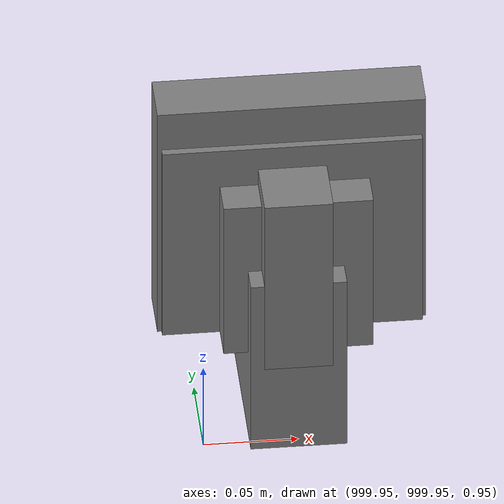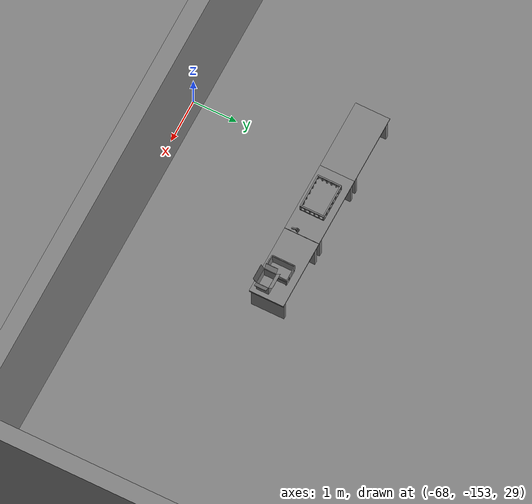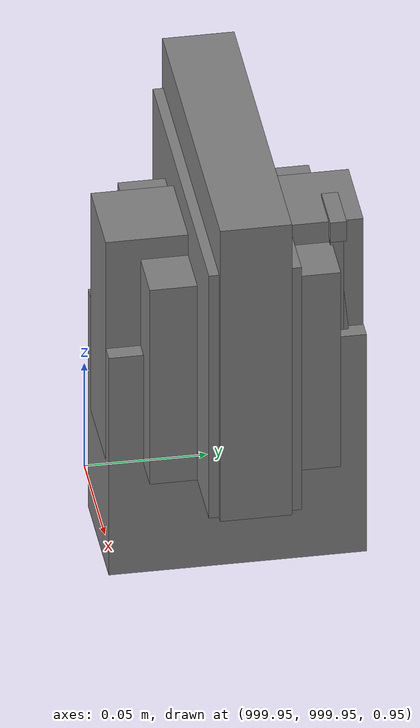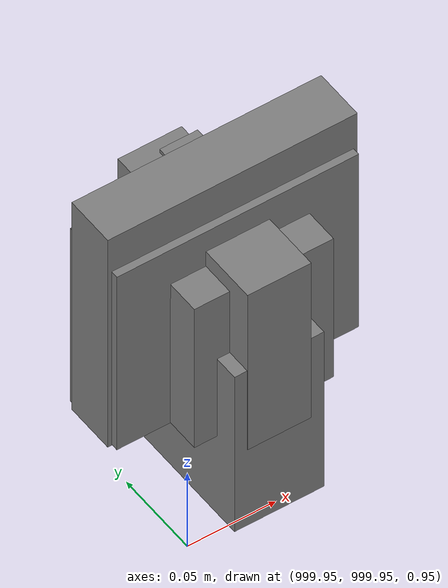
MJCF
<mujoco>
    <option gravity="0.000000000 0.000000000 -9.810000420" timestep="0.0049999999" integrator="implicitfast" density="1.225" viscosity="1.8000001e-05" noslip_iterations="10" iterations="100" sdf_iterations="50">
        <flag multiccd="disable"/>
    </option>
    <size memory="1000M"/>
    <compiler coordinate="local"/>
    <worldbody>
        <light cutoff="30" pos="0 1 1" dir="0 -1 -2"/>
        <light cutoff="30" pos="0 -1 1" dir="0 1 -2"/>
        <body pos="-64.866622925 -149.383972168 30.183746338" euler="89.999984741 89.999946594 0.000000000" name="openloong_gripper_2f85_fix_base_usda_bluebox_01">
            <geom contype="1" conaffinity="1" density="1000" type="box" material="" rgba="0.500000000 0.500000000 0.500000000 1.000000000" solimp="0.899999976 0.949999988 0.001000000" friction="1.000000000 0.005000000 0.000100000" solref="0.020000000 1.000000000" margin="0" condim="3" group="0" pos="0.276580811 0.187225342 0.000068665" quat="0.707106948 0.000077471 0.707106352 0.000077486" size="0.100000001 0.057999998 0.010000000" name="openloong_gripper_2f85_fix_base_usda_geom_FB6A63C0_ED59_477A_85FF_AAF391F5D108"/>
            <geom contype="1" conaffinity="1" density="1000" type="box" material="" rgba="0.500000000 0.500000000 0.500000000 1.000000000" solimp="0.899999976 0.949999988 0.001000000" friction="1.000000000 0.005000000 0.000100000" solref="0.020000000 1.000000000" margin="0" condim="3" group="0" pos="0.000000000 0.002883911 0.000000000" quat="0.999999881 0.000000000 0.000000000 0.000000000" size="0.254000008 0.003000000 0.172000006" name="openloong_gripper_2f85_fix_base_usda_geom_891953E2_4AC2_4312_A1DF_9480A01B147F"/>
            <geom contype="1" conaffinity="1" density="1000" type="box" material="" rgba="0.500000000 0.500000000 0.500000000 1.000000000" solimp="0.899999976 0.949999988 0.001000000" friction="1.000000000 0.005000000 0.000100000" solref="0.020000000 1.000000000" margin="0" condim="3" group="0" pos="0.000000000 0.124874115 0.173484802" quat="0.999796331 0.020176515 -0.000000015 0.000000030" size="0.259999990 0.119999997 0.007000000" name="openloong_gripper_2f85_fix_base_usda_geom_57A227EB_34C0_4F8B_8F18_470882F73B1E"/>
            <geom contype="1" conaffinity="1" density="1000" type="box" material="" rgba="0.500000000 0.500000000 0.500000000 1.000000000" solimp="0.899999976 0.949999988 0.001000000" friction="1.000000000 0.005000000 0.000100000" solref="0.020000000 1.000000000" margin="0" condim="3" group="0" pos="0.000000000 0.124874115 -0.173469543" quat="0.999796331 -0.020176545 -0.000000015 0.000000000" size="0.259999990 0.119999997 0.007000000" name="openloong_gripper_2f85_fix_base_usda_geom_81F08663_940D_484F_A97E_80766AC8F83D"/>
            <geom contype="1" conaffinity="1" density="1000" type="box" material="" rgba="0.500000000 0.500000000 0.500000000 1.000000000" solimp="0.899999976 0.949999988 0.001000000" friction="1.000000000 0.005000000 0.000100000" solref="0.020000000 1.000000000" margin="0" condim="3" group="0" pos="0.000000000 0.214008331 0.188980103" quat="0.999912977 0.013176724 0.000000015 0.000000000" size="0.259999990 0.029999999 0.012500000" name="openloong_gripper_2f85_fix_base_usda_geom_15919A1A_FCBE_49DE_B51F_51EDFA0D06FF"/>
            <geom contype="1" conaffinity="1" density="1000" type="box" material="" rgba="0.500000000 0.500000000 0.500000000 1.000000000" solimp="0.899999976 0.949999988 0.001000000" friction="1.000000000 0.005000000 0.000100000" solref="0.020000000 1.000000000" margin="0" condim="3" group="0" pos="-0.258361816 0.125289917 0.001876831" quat="0.702796936 -0.020792112 0.710783124 0.020769298" size="0.189999998 0.119999997 0.009000000" name="openloong_gripper_2f85_fix_base_usda_geom_C48E348C_EEFB_4468_9342_68CACE077900"/>
            <geom contype="1" conaffinity="1" density="1000" type="box" material="" rgba="0.500000000 0.500000000 0.500000000 1.000000000" solimp="0.899999976 0.949999988 0.001000000" friction="1.000000000 0.005000000 0.000100000" solref="0.020000000 1.000000000" margin="0" condim="3" group="0" pos="0.000000000 0.214008331 -0.188980103" quat="0.999912977 -0.013176769 0.000000030 0.000000015" size="0.259999990 0.029999999 0.012500000" name="openloong_gripper_2f85_fix_base_usda_geom_E9DAFA6C_085D_4D8A_B7F4_996B3289A587"/>
            <geom contype="1" conaffinity="1" density="1000" type="box" material="" rgba="0.500000000 0.500000000 0.500000000 1.000000000" solimp="0.899999976 0.949999988 0.001000000" friction="1.000000000 0.005000000 0.000100000" solref="0.020000000 1.000000000" margin="0" condim="3" group="0" pos="-0.276611328 0.187225342 0.000068665" quat="0.707106650 0.000077441 0.707106709 0.000077456" size="0.100000001 0.057999998 0.010000000" name="openloong_gripper_2f85_fix_base_usda_geom_2C2DD6FB_F2EC_4656_8FF8_FE40EEE3E02C"/>
            <geom contype="1" conaffinity="1" density="1000" type="box" material="" rgba="0.500000000 0.500000000 0.500000000 1.000000000" solimp="0.899999976 0.949999988 0.001000000" friction="1.000000000 0.005000000 0.000100000" solref="0.020000000 1.000000000" margin="0" condim="3" group="0" pos="0.258331299 0.125289917 0.001876831" quat="0.702851415 0.018856421 0.710823774 -0.019329369" size="0.189999998 0.119999997 0.009000000" name="openloong_gripper_2f85_fix_base_usda_geom_F1F25483_DDD5_4A18_B033_46F80BEF28EE"/>
            <freejoint name="openloong_gripper_2f85_fix_base_usda_bluebox_01_joint"/>
            <site size="0.005000000 0.005000000 0.005000000" rgba="0.500000000 0.500000000 0.500000000 1.000000000" pos="0.000000000 0.000000000 0.000000000" quat="0.999961913 0.008726534 0.000000000 0.000000000" group="0" type="sphere" name="openloong_gripper_2f85_fix_base_usda_bluebox_01site"/>
        </body>
        <body pos="-64.496299744 -149.491867065 30.235729218" euler="0.000000000 0.000000000 89.999946594" name="openloong_gripper_2f85_fix_base_usda_cardboardbox_01">
            <geom contype="1" conaffinity="1" density="1000" type="box" material="" rgba="0.500000000 0.500000000 0.500000000 1.000000000" solimp="0.899999976 0.949999988 0.001000000" friction="1.000000000 0.005000000 0.000100000" solref="0.020000000 1.000000000" margin="0" condim="3" group="0" pos="-0.003166199 -0.004086494 0.005052090" quat="1.000000000 0.000000000 0.000000000 0.000000000" size="0.142499998 0.177500010 0.005000000" name="openloong_gripper_2f85_fix_base_usda_geom_0BCC0E4E_7054_4A24_90AA_6955F8A7DB12"/>
            <geom contype="1" conaffinity="1" density="1000" type="box" material="" rgba="0.500000000 0.500000000 0.500000000 1.000000000" solimp="0.899999976 0.949999988 0.001000000" friction="1.000000000 0.005000000 0.000100000" solref="0.020000000 1.000000000" margin="0" condim="3" group="0" pos="-0.003166199 0.170316696 0.150570869" quat="1.000000000 0.000000000 0.000000000 0.000000000" size="0.142499998 0.005000000 0.149999991" name="openloong_gripper_2f85_fix_base_usda_geom_8CB45CDC_AC03_4159_B2A5_A5C3369F93D8"/>
            <geom contype="1" conaffinity="1" density="1000" type="box" material="" rgba="0.500000000 0.500000000 0.500000000 1.000000000" solimp="0.899999976 0.949999988 0.001000000" friction="1.000000000 0.005000000 0.000100000" solref="0.020000000 1.000000000" margin="0" condim="3" group="0" pos="-0.147399902 -0.005307198 0.150570869" quat="1.000000000 0.000000000 0.000000000 0.000000000" size="0.005000000 0.177500010 0.149999991" name="openloong_gripper_2f85_fix_base_usda_geom_2D2D5280_87E8_442C_BA4A_52E07F2AD507"/>
            <geom contype="1" conaffinity="1" density="1000" type="box" material="" rgba="0.500000000 0.500000000 0.500000000 1.000000000" solimp="0.899999976 0.949999988 0.001000000" friction="1.000000000 0.005000000 0.000100000" solref="0.020000000 1.000000000" margin="0" condim="3" group="0" pos="0.140275955 -0.005307198 0.150570869" quat="1.000000000 0.000000000 0.000000000 0.000000000" size="0.005000000 0.177500010 0.149999991" name="openloong_gripper_2f85_fix_base_usda_geom_93473E97_9E1D_405B_B186_BB4D30DC94A4"/>
            <geom contype="1" conaffinity="1" density="1000" type="box" material="" rgba="0.500000000 0.500000000 0.500000000 1.000000000" solimp="0.899999976 0.949999988 0.001000000" friction="1.000000000 0.005000000 0.000100000" solref="0.020000000 1.000000000" margin="0" condim="3" group="0" pos="-0.003166199 -0.181550980 0.150570869" quat="1.000000000 0.000000000 0.000000000 0.000000000" size="0.142499998 0.005000000 0.149999991" name="openloong_gripper_2f85_fix_base_usda_geom_7801B2BD_067D_4CA9_B5B7_205038005AA9"/>
            <freejoint name="openloong_gripper_2f85_fix_base_usda_cardboardbox_01_joint"/>
            <site size="0.005000000 0.005000000 0.005000000" rgba="0.500000000 0.500000000 0.500000000 1.000000000" pos="0.000000000 0.000000000 0.000000000" quat="0.999961913 0.008726535 0.000000000 0.000000000" group="0" type="sphere" name="openloong_gripper_2f85_fix_base_usda_site_A7053DD0_F69C_4BCF_AA28_9E80F98F81A6"/>
            <body pos="0.139160156 -0.004048347 0.301930904" euler="-179.999954224 49.383502960 179.999954224" name="openloong_gripper_2f85_fix_base_usda_A1_006">
                <geom contype="1" conaffinity="1" density="1000" type="box" material="" rgba="0.500000000 0.500000000 0.500000000 1.000000000" solimp="0.899999976 0.949999988 0.001000000" friction="1.000000000 0.005000000 0.000100000" solref="0.020000000 1.000000000" margin="0" condim="3" group="0" pos="-0.071587563 0.000009537 0.001745224" quat="0.999999881 0.000000000 0.000000000 0.000000000" size="0.071249999 0.179999992 0.002500000" name="openloong_gripper_2f85_fix_base_usda_geom_40AE80F0_F1D6_45D2_81DF_0EA3AC68786B"/>
                <joint armature="0" stiffness="0.07" damping="0.0099999998" axis="0.000000 1.000000 0.000000" type="hinge" name="openloong_gripper_2f85_fix_base_usda_A1_006"/>
            </body>
            <body pos="-0.145902634 -0.004086494 0.301938057" euler="-180.000000000 -60.000011444 -180.000000000" name="openloong_gripper_2f85_fix_base_usda_A2_006">
                <geom contype="1" conaffinity="1" density="1000" type="box" material="" rgba="0.500000000 0.500000000 0.500000000 1.000000000" solimp="0.899999976 0.949999988 0.001000000" friction="1.000000000 0.005000000 0.000100000" solref="0.020000000 1.000000000" margin="0" condim="3" group="0" pos="0.071268082 0.000009537 0.002717972" quat="0.000002921 0.000000000 -0.000000030 0.999999881" size="0.071249999 0.179999992 0.002500000" name="openloong_gripper_2f85_fix_base_usda_geom_32C95699_5F09_4086_A9A0_A88C93BA9898"/>
                <joint armature="0" stiffness="0.07" damping="0.0099999998" axis="0.000000 1.000000 0.000000" type="hinge" name="openloong_gripper_2f85_fix_base_usda_A2_006"/>
            </body>
            <body pos="-0.003385544 0.175991058 0.301930904" euler="-125.858116150 -0.000004561 0.000002331" name="openloong_gripper_2f85_fix_base_usda_B2_006">
                <geom contype="1" conaffinity="1" density="1000" type="box" material="" rgba="0.500000000 0.500000000 0.500000000 1.000000000" solimp="0.899999976 0.949999988 0.001000000" friction="1.000000000 0.005000000 0.000100000" solref="0.020000000 1.000000000" margin="0" condim="3" group="0" pos="0.000009537 -0.070939064 -0.002470016" quat="0.999614120 0.027776197 -0.000000015 0.000000030" size="0.137500003 0.064999998 0.005000000" name="openloong_gripper_2f85_fix_base_usda_geom_4FA074C8_B23C_4265_85DD_571DE7E9D176"/>
                <joint armature="0" stiffness="0.07" damping="0.0099999998" axis="1.000000 0.000000 0.000000" type="hinge" name="openloong_gripper_2f85_fix_base_usda_B2_006"/>
            </body>
            <body pos="-0.003385544 -0.184140205 0.301938057" euler="147.805557251 0.000000000 0.000000000" name="openloong_gripper_2f85_fix_base_usda_B1_006">
                <geom contype="1" conaffinity="1" density="1000" type="box" material="" rgba="0.500000000 0.500000000 0.500000000 1.000000000" solimp="0.899999976 0.949999988 0.001000000" friction="1.000000000 0.005000000 0.000100000" solref="0.020000000 1.000000000" margin="0" condim="3" group="0" pos="-0.000028610 0.070202351 -0.002703667" quat="0.999614179 -0.027776167 0.000000000 0.000000000" size="0.137500003 0.064999998 0.005000000" name="openloong_gripper_2f85_fix_base_usda_geom_F0B4D244_4D83_43E2_932A_244465CF195F"/>
                <joint armature="0" stiffness="0.07" damping="0.0099999998" axis="1.000000 0.000000 0.000000" type="hinge" name="openloong_gripper_2f85_fix_base_usda_B1_006"/>
            </body>
        </body>
        <body pos="-65.882858276 -149.481979370 30.229999542" euler="-64.487716675 0.000000000 0.000000000" name="openloong_gripper_2f85_fix_base_usda_Barcode">
            <geom contype="1" conaffinity="1" density="1000" type="box" material="" rgba="0.500000000 0.500000000 0.500000000 1.000000000" solimp="0.899999976 0.949999988 0.001000000" friction="1.000000000 0.005000000 0.000100000" solref="0.020000000 1.000000000" margin="0" condim="3" group="0" pos="0.000000000 0.013038635 0.001419067" quat="0.000000000 0.000000000 0.000000000 1.000000119" size="0.034000002 0.010000000 0.017999999" name="openloong_gripper_2f85_fix_base_usda_geom_DA57E306_FB7E_4B2C_AD57_DB72631657C0"/>
            <geom contype="1" conaffinity="1" density="1000" type="box" material="" rgba="0.500000000 0.500000000 0.500000000 1.000000000" solimp="0.899999976 0.949999988 0.001000000" friction="1.000000000 0.005000000 0.000100000" solref="0.020000000 1.000000000" margin="0" condim="3" group="0" pos="0.000000000 -0.035301208 -0.007095337" quat="0.000000000 0.000000000 -0.043619365 0.999048233" size="0.028999999 0.010000000 0.020000000" name="openloong_gripper_2f85_fix_base_usda_geom_DE0E43C5_CFC7_4EE6_82D5_C0CDBF1C2955"/>
            <geom contype="1" conaffinity="1" density="1000" type="box" material="" rgba="0.500000000 0.500000000 0.500000000 1.000000000" solimp="0.899999976 0.949999988 0.001000000" friction="1.000000000 0.005000000 0.000100000" solref="0.020000000 1.000000000" margin="0" condim="3" group="0" pos="0.000000000 -0.043411255 -0.011749268" quat="0.922262907 0.386563420 0.000000000 0.000000000" size="0.026000001 0.010000000 0.020000000" name="openloong_gripper_2f85_fix_base_usda_geom_36CA37DD_065D_49AB_9980_969CBD8B7F9E"/>
            <geom contype="1" conaffinity="1" density="1000" type="box" material="" rgba="0.500000000 0.500000000 0.500000000 1.000000000" solimp="0.899999976 0.949999988 0.001000000" friction="1.000000000 0.005000000 0.000100000" solref="0.020000000 1.000000000" margin="0" condim="3" group="0" pos="0.000000000 -0.016967773 -0.031860352" quat="0.000000000 0.000000000 0.000000000 1.000000119" size="0.008000000 0.010000000 0.013000000" name="openloong_gripper_2f85_fix_base_usda_geom_AA1342E6_8203_4254_BFED_92580213AB11"/>
            <geom contype="1" conaffinity="1" density="1000" type="box" material="" rgba="0.500000000 0.500000000 0.500000000 1.000000000" solimp="0.899999976 0.949999988 0.001000000" friction="1.000000000 0.005000000 0.000100000" solref="0.020000000 1.000000000" margin="0" condim="3" group="0" pos="0.000000000 -0.001869202 0.000312805" quat="0.953716993 0.300705761 0.000000000 0.000000000" size="0.032000002 0.010000000 0.018999999" name="openloong_gripper_2f85_fix_base_usda_geom_1818A77C_BE17_4E38_AFB5_C5AB4EEA421C"/>
            <geom contype="1" conaffinity="1" density="1000" type="box" material="" rgba="0.500000000 0.500000000 0.500000000 1.000000000" solimp="0.899999976 0.949999988 0.001000000" friction="1.000000000 0.005000000 0.000100000" solref="0.020000000 1.000000000" margin="0" condim="3" group="0" pos="0.000000000 -0.019531250 -0.003173828" quat="0.953716993 0.300705761 0.000000000 0.000000000" size="0.030999999 0.010000000 0.020000000" name="openloong_gripper_2f85_fix_base_usda_geom_9D5CE12A_7543_48E4_860E_FC56CB2BE60A"/>
            <geom contype="1" conaffinity="1" density="1000" type="box" material="" rgba="0.500000000 0.500000000 0.500000000 1.000000000" solimp="0.899999976 0.949999988 0.001000000" friction="1.000000000 0.005000000 0.000100000" solref="0.020000000 1.000000000" margin="0" condim="3" group="0" pos="0.000000000 -0.035301208 -0.007095337" quat="0.953716993 0.300705761 0.000000000 0.000000000" size="0.028999999 0.010000000 0.020000000" name="openloong_gripper_2f85_fix_base_usda_geom_636E9B13_8A8D_44C6_A7DF_BD191EA89B30"/>
            <geom contype="1" conaffinity="1" density="1000" type="box" material="" rgba="0.500000000 0.500000000 0.500000000 1.000000000" solimp="0.899999976 0.949999988 0.001000000" friction="1.000000000 0.005000000 0.000100000" solref="0.020000000 1.000000000" margin="0" condim="3" group="0" pos="0.000000000 -0.042617798 -0.071121216" quat="0.000000000 0.000000000 0.000000000 1.000000119" size="0.013000000 0.021000000 0.059999999" name="openloong_gripper_2f85_fix_base_usda_geom_AF3C377F_7E3E_48C5_A9E8_872842AF8023"/>
            <freejoint name="openloong_gripper_2f85_fix_base_usda_Barcode_joint"/>
            <site size="0.005000000 0.005000000 0.005000000" rgba="0.500000000 0.500000000 0.500000000 1.000000000" pos="0.000000000 0.000000000 0.000000000" quat="1.000000000 0.000000000 0.000000000 0.000000000" group="0" type="sphere" name="openloong_gripper_2f85_fix_base_usda_Barcode_site"/>
        </body>
        <body pos="-66.745018005 -149.392349243 30.184000015" euler="0.000000000 0.000000000 89.999946594" name="[22332576404311]_Basket_01">
            <geom contype="1" conaffinity="1" density="1000" type="box" material="" rgba="0.500000000 0.500000000 0.500000000 1.000000000" solimp="0.899999976 0.949999988 0.001000000" friction="1.000000000 0.005000000 0.000100000" solref="0.020000000 1.000000000" margin="0" condim="3" group="0" pos="-0.052425385 0.389207840 0.089787483" quat="0.707107008 0.000000000 0.000000000 0.707106411" size="0.014249999 0.014249999 0.059999999" name="[22332576404311]_geom_05B5F737_7FE7_4BF4_BFA8_CC38E531A839"/>
            <geom contype="1" conaffinity="1" density="1000" type="box" material="" rgba="0.500000000 0.500000000 0.500000000 1.000000000" solimp="0.899999976 0.949999988 0.001000000" friction="1.000000000 0.005000000 0.000100000" solref="0.020000000 1.000000000" margin="0" condim="3" group="0" pos="0.264015198 -0.133043289 0.089787483" quat="0.707107008 0.000000000 0.000000000 0.707106411" size="0.014249999 0.014249999 0.059999999" name="[22332576404311]_geom_CD4D122E_8E1F_467C_85A1_872C7A11B9C6"/>
            <geom contype="1" conaffinity="1" density="1000" type="box" material="" rgba="0.500000000 0.500000000 0.500000000 1.000000000" solimp="0.899999976 0.949999988 0.001000000" friction="1.000000000 0.005000000 0.000100000" solref="0.020000000 1.000000000" margin="0" condim="3" group="0" pos="-0.264015198 -0.265548706 0.089793205" quat="0.707107008 0.000000000 0.000000000 0.707106411" size="0.014249999 0.014249999 0.059999999" name="[22332576404311]_geom_FF715350_121A_45C7_BC3A_3253602764BF"/>
            <geom contype="1" conaffinity="1" density="1000" type="box" material="" rgba="0.500000000 0.500000000 0.500000000 1.000000000" solimp="0.899999976 0.949999988 0.001000000" friction="1.000000000 0.005000000 0.000100000" solref="0.020000000 1.000000000" margin="0" condim="3" group="0" pos="-0.160263062 -0.389322281 0.089793205" quat="0.707107008 0.000000000 0.000000000 0.707106411" size="0.014249999 0.014249999 0.059999999" name="[22332576404311]_geom_8AF8C9B2_CD63_48F4_91D3_74A9D8EEB92D"/>
            <geom contype="1" conaffinity="1" density="1000" type="box" material="" rgba="0.500000000 0.500000000 0.500000000 1.000000000" solimp="0.899999976 0.949999988 0.001000000" friction="1.000000000 0.005000000 0.000100000" solref="0.020000000 1.000000000" margin="0" condim="3" group="0" pos="0.162265778 -0.389322281 0.089787483" quat="0.707107008 0.000000000 0.000000000 0.707106411" size="0.014249999 0.014249999 0.059999999" name="[22332576404311]_geom_F790D2BD_6922_4ACE_BE62_B18B6819D840"/>
            <geom contype="1" conaffinity="1" density="1000" type="box" material="" rgba="0.500000000 0.500000000 0.500000000 1.000000000" solimp="0.899999976 0.949999988 0.001000000" friction="1.000000000 0.005000000 0.000100000" solref="0.020000000 1.000000000" margin="0" condim="3" group="0" pos="0.264015198 0.389207840 0.089787483" quat="0.707107008 0.000000000 0.000000000 0.707106411" size="0.014249999 0.014249999 0.059999999" name="[22332576404311]_geom_715E865A_C035_4066_82D2_13BE74E77AD3"/>
            <geom contype="1" conaffinity="1" density="1000" type="box" material="" rgba="0.500000000 0.500000000 0.500000000 1.000000000" solimp="0.899999976 0.949999988 0.001000000" friction="1.000000000 0.005000000 0.000100000" solref="0.020000000 1.000000000" margin="0" condim="3" group="0" pos="-0.264015198 -0.133043289 0.089793205" quat="0.707107008 0.000000000 0.000000000 0.707106411" size="0.014249999 0.014249999 0.059999999" name="[22332576404311]_geom_375CE715_24BA_4743_AB0C_84B1F883240E"/>
            <geom contype="1" conaffinity="1" density="1000" type="box" material="" rgba="0.500000000 0.500000000 0.500000000 1.000000000" solimp="0.899999976 0.949999988 0.001000000" friction="1.000000000 0.005000000 0.000100000" solref="0.020000000 1.000000000" margin="0" condim="3" group="0" pos="-0.264026642 0.269256592 0.089793205" quat="0.707107008 0.000000000 0.000000000 0.707106411" size="0.014249999 0.014249999 0.059999999" name="[22332576404311]_geom_EBF34943_4D96_4FF2_8D06_ECDE957941C2"/>
            <geom contype="1" conaffinity="1" density="1000" type="box" material="" rgba="0.500000000 0.500000000 0.500000000 1.000000000" solimp="0.899999976 0.949999988 0.001000000" friction="1.000000000 0.005000000 0.000100000" solref="0.020000000 1.000000000" margin="0" condim="3" group="0" pos="0.054462433 0.389207840 0.089787483" quat="0.707107008 0.000000000 0.000000000 0.707106411" size="0.014249999 0.014249999 0.059999999" name="[22332576404311]_geom_B753196B_A3EC_4233_B666_D421D656D8CA"/>
            <geom contype="1" conaffinity="1" density="1000" type="box" material="" rgba="0.500000000 0.500000000 0.500000000 1.000000000" solimp="0.899999976 0.949999988 0.001000000" friction="1.000000000 0.005000000 0.000100000" solref="0.020000000 1.000000000" margin="0" condim="3" group="0" pos="0.054462433 -0.389322281 0.089787483" quat="0.707107008 0.000000000 0.000000000 0.707106411" size="0.014249999 0.014249999 0.059999999" name="[22332576404311]_geom_18EEEBEB_8220_4E95_928F_EF7AC8ED403A"/>
            <geom contype="1" conaffinity="1" density="1000" type="box" material="" rgba="0.500000000 0.500000000 0.500000000 1.000000000" solimp="0.899999976 0.949999988 0.001000000" friction="1.000000000 0.005000000 0.000100000" solref="0.020000000 1.000000000" margin="0" condim="3" group="0" pos="0.264015198 0.269256592 0.089793205" quat="0.707107008 0.000000000 0.000000000 0.707106411" size="0.014249999 0.014249999 0.059999999" name="[22332576404311]_geom_06E2506F_52C6_41C1_818A_CE6AAE70688B"/>
            <geom contype="1" conaffinity="1" density="1000" type="box" material="" rgba="0.500000000 0.500000000 0.500000000 1.000000000" solimp="0.899999976 0.949999988 0.001000000" friction="1.000000000 0.005000000 0.000100000" solref="0.020000000 1.000000000" margin="0" condim="3" group="0" pos="0.264015198 -0.389322281 0.089787483" quat="0.707107008 0.000000000 0.000000000 0.707106411" size="0.014249999 0.014249999 0.059999999" name="[22332576404311]_geom_384D3EE7_D4E1_4267_AF29_CC9D9140135C"/>
            <geom contype="1" conaffinity="1" density="1000" type="box" material="" rgba="0.500000000 0.500000000 0.500000000 1.000000000" solimp="0.899999976 0.949999988 0.001000000" friction="1.000000000 0.005000000 0.000100000" solref="0.020000000 1.000000000" margin="0" condim="3" group="0" pos="0.000000000 0.000000000 0.015998840" quat="0.707107008 0.000000000 0.000000000 0.707106411" size="0.403499991 0.279000014 0.015750000" name="[22332576404311]_geom_804439F8_64C1_46AE_9823_0F5997C7763A"/>
            <geom contype="1" conaffinity="1" density="1000" type="box" material="" rgba="0.500000000 0.500000000 0.500000000 1.000000000" solimp="0.899999976 0.949999988 0.001000000" friction="1.000000000 0.005000000 0.000100000" solref="0.020000000 1.000000000" margin="0" condim="3" group="0" pos="0.000000000 -0.389476776 0.163619041" quat="0.707107008 0.000000000 0.000000000 0.707106411" size="0.015000000 0.277500004 0.015750000" name="[22332576404311]_geom_EEB243D3_BF87_49C0_90AA_E571AE6D3357"/>
            <geom contype="1" conaffinity="1" density="1000" type="box" material="" rgba="0.500000000 0.500000000 0.500000000 1.000000000" solimp="0.899999976 0.949999988 0.001000000" friction="1.000000000 0.005000000 0.000100000" solref="0.020000000 1.000000000" margin="0" condim="3" group="0" pos="0.162265778 0.389207840 0.089787483" quat="0.707107008 0.000000000 0.000000000 0.707106411" size="0.014249999 0.014249999 0.059999999" name="[22332576404311]_geom_8BDF85FF_BB9C_4C48_AAA3_F547BB267CD8"/>
            <geom contype="1" conaffinity="1" density="1000" type="box" material="" rgba="0.500000000 0.500000000 0.500000000 1.000000000" solimp="0.899999976 0.949999988 0.001000000" friction="1.000000000 0.005000000 0.000100000" solref="0.020000000 1.000000000" margin="0" condim="3" group="0" pos="0.000000000 0.389471054 0.163619041" quat="0.707107008 0.000000000 0.000000000 0.707106411" size="0.015000000 0.277500004 0.015750000" name="[22332576404311]_geom_4A3F7ADF_43B7_4FA6_97DA_C0A3738B6C1A"/>
            <geom contype="1" conaffinity="1" density="1000" type="box" material="" rgba="0.500000000 0.500000000 0.500000000 1.000000000" solimp="0.899999976 0.949999988 0.001000000" friction="1.000000000 0.005000000 0.000100000" solref="0.020000000 1.000000000" margin="0" condim="3" group="0" pos="-0.263511658 0.000000000 0.163619041" quat="0.707107008 0.000000000 0.000000000 0.707106411" size="0.403499991 0.015000000 0.015750000" name="[22332576404311]_geom_DA4C128F_B731_4C49_AC57_155D118B2647"/>
            <geom contype="1" conaffinity="1" density="1000" type="box" material="" rgba="0.500000000 0.500000000 0.500000000 1.000000000" solimp="0.899999976 0.949999988 0.001000000" friction="1.000000000 0.005000000 0.000100000" solref="0.020000000 1.000000000" margin="0" condim="3" group="0" pos="-0.264015198 0.141334534 0.089793205" quat="0.707107008 0.000000000 0.000000000 0.707106411" size="0.014249999 0.014249999 0.059999999" name="[22332576404311]_geom_9836FC3B_595B_4933_A2BE_3294E37BBF3D"/>
            <geom contype="1" conaffinity="1" density="1000" type="box" material="" rgba="0.500000000 0.500000000 0.500000000 1.000000000" solimp="0.899999976 0.949999988 0.001000000" friction="1.000000000 0.005000000 0.000100000" solref="0.020000000 1.000000000" margin="0" condim="3" group="0" pos="0.264015198 -0.265548706 0.089787483" quat="0.707107008 0.000000000 0.000000000 0.707106411" size="0.014249999 0.014249999 0.059999999" name="[22332576404311]_geom_771F0A31_0A91_454A_98F5_90DC2915406D"/>
            <geom contype="1" conaffinity="1" density="1000" type="box" material="" rgba="0.500000000 0.500000000 0.500000000 1.000000000" solimp="0.899999976 0.949999988 0.001000000" friction="1.000000000 0.005000000 0.000100000" solref="0.020000000 1.000000000" margin="0" condim="3" group="0" pos="-0.160263062 0.389207840 0.089787483" quat="0.707107008 0.000000000 0.000000000 0.707106411" size="0.014249999 0.014249999 0.059999999" name="[22332576404311]_geom_828998D4_2C1A_4484_96CE_6B4F6B149FC3"/>
            <geom contype="1" conaffinity="1" density="1000" type="box" material="" rgba="0.500000000 0.500000000 0.500000000 1.000000000" solimp="0.899999976 0.949999988 0.001000000" friction="1.000000000 0.005000000 0.000100000" solref="0.020000000 1.000000000" margin="0" condim="3" group="0" pos="-0.052425385 -0.389322281 0.089787483" quat="0.707107008 0.000000000 0.000000000 0.707106411" size="0.014249999 0.014249999 0.059999999" name="[22332576404311]_geom_6CD8B228_B8C4_44CE_9679_83B0A88B8F87"/>
            <geom contype="1" conaffinity="1" density="1000" type="box" material="" rgba="0.500000000 0.500000000 0.500000000 1.000000000" solimp="0.899999976 0.949999988 0.001000000" friction="1.000000000 0.005000000 0.000100000" solref="0.020000000 1.000000000" margin="0" condim="3" group="0" pos="-0.264026642 -0.389322281 0.089793205" quat="0.707107008 0.000000000 0.000000000 0.707106411" size="0.014249999 0.014249999 0.059999999" name="[22332576404311]_geom_42D8C516_F3F5_4DA1_AFB6_3FD2A09AAD44"/>
            <geom contype="1" conaffinity="1" density="1000" type="box" material="" rgba="0.500000000 0.500000000 0.500000000 1.000000000" solimp="0.899999976 0.949999988 0.001000000" friction="1.000000000 0.005000000 0.000100000" solref="0.020000000 1.000000000" margin="0" condim="3" group="0" pos="0.264015198 0.141334534 0.089787483" quat="0.707107008 0.000000000 0.000000000 0.707106411" size="0.014249999 0.014249999 0.059999999" name="[22332576404311]_geom_E8DB0CF1_339E_4BD2_A617_BE3FD51B9E40"/>
            <geom contype="1" conaffinity="1" density="1000" type="box" material="" rgba="0.500000000 0.500000000 0.500000000 1.000000000" solimp="0.899999976 0.949999988 0.001000000" friction="1.000000000 0.005000000 0.000100000" solref="0.020000000 1.000000000" margin="0" condim="3" group="0" pos="-0.264015198 0.389207840 0.089793205" quat="0.707107008 0.000000000 0.000000000 0.707106411" size="0.014249999 0.014249999 0.059999999" name="[22332576404311]_geom_FAD5CB9B_05B2_4446_8886_CE309775F4C4"/>
            <geom contype="1" conaffinity="1" density="1000" type="box" material="" rgba="0.500000000 0.500000000 0.500000000 1.000000000" solimp="0.899999976 0.949999988 0.001000000" friction="1.000000000 0.005000000 0.000100000" solref="0.020000000 1.000000000" margin="0" condim="3" group="0" pos="0.264015198 0.004480362 0.089787483" quat="0.707107008 0.000000000 0.000000000 0.707106411" size="0.014249999 0.014249999 0.059999999" name="[22332576404311]_geom_634AAE03_1097_4EC0_9E7F_DBEB94A1C6C4"/>
            <geom contype="1" conaffinity="1" density="1000" type="box" material="" rgba="0.500000000 0.500000000 0.500000000 1.000000000" solimp="0.899999976 0.949999988 0.001000000" friction="1.000000000 0.005000000 0.000100000" solref="0.020000000 1.000000000" margin="0" condim="3" group="0" pos="0.263694763 -0.000011444 0.163619041" quat="0.707107008 0.000000000 0.000000000 0.707106411" size="0.403499991 0.015000000 0.015750000" name="[22332576404311]_geom_8FA87577_B7B7_496F_9652_8D73A4B01F6C"/>
            <geom contype="1" conaffinity="1" density="1000" type="box" material="" rgba="0.500000000 0.500000000 0.500000000 1.000000000" solimp="0.899999976 0.949999988 0.001000000" friction="1.000000000 0.005000000 0.000100000" solref="0.020000000 1.000000000" margin="0" condim="3" group="0" pos="-0.264015198 0.004480362 0.089793205" quat="0.707107008 0.000000000 0.000000000 0.707106411" size="0.014249999 0.014249999 0.059999999" name="[22332576404311]_geom_70010C60_C1C6_40C3_83D1_9D85469D5861"/>
            <freejoint name="[22332576404311]_joint_34D61D91_780E_45F2_8F51_DD0D13D30A33"/>
        </body>
        <body pos="0.000000000 0.000000000 0.000000000" euler="0.000000000 0.000000000 0.000000000" name="Static Objects_Static Objects">
            <geom contype="1" conaffinity="1" density="1000" type="box" material="" rgba="0.500000000 0.500000000 0.500000000 1.000000000" solimp="0.899999976 0.949999988 0.001000000" friction="1.000000000 0.005000000 0.000100000" solref="0.020000000 1.000000000" margin="0" condim="3" group="0" pos="-67.544113159 -149.365814209 29.727830887" quat="0.500000417 0.499999970 0.499999553 0.499999970" size="0.381000012 0.319999993 0.041000001" name="Static Objects_geom_6EC21CCE_F7AE_42FA_A6E1_1AAEB15A5B4E"/>
            <geom contype="1" conaffinity="1" density="1000" type="box" material="" rgba="0.500000000 0.500000000 0.500000000 1.000000000" solimp="0.899999976 0.949999988 0.001000000" friction="1.000000000 0.005000000 0.000100000" solref="0.020000000 1.000000000" margin="0" condim="3" group="0" pos="-68.239501953 -149.365814209 30.086868286" quat="0.500000417 0.499999970 0.499999553 0.499999970" size="0.370999992 0.039500002 0.745000005" name="Static Objects_geom_A5A48765_CD4A_4683_9C51_9683E6A2F75A"/>
            <geom contype="1" conaffinity="1" density="1000" type="box" material="" rgba="0.500000000 0.500000000 0.500000000 1.000000000" solimp="0.899999976 0.949999988 0.001000000" friction="1.000000000 0.005000000 0.000100000" solref="0.020000000 1.000000000" margin="0" condim="3" group="0" pos="-68.239501953 -149.365814209 30.147235870" quat="0.500000417 0.499999970 0.499999553 0.499999970" size="0.400000006 0.022000000 0.800000012" name="Static Objects_geom_E5BBB55F_5680_419D_B336_422E2BAF8248"/>
            <geom contype="1" conaffinity="1" density="1000" type="box" material="" rgba="0.500000000 0.500000000 0.500000000 1.000000000" solimp="0.899999976 0.949999988 0.001000000" friction="1.000000000 0.005000000 0.000100000" solref="0.020000000 1.000000000" margin="0" condim="3" group="0" pos="-68.934890747 -149.365814209 29.727830887" quat="0.500000417 0.499999970 0.499999553 0.499999970" size="0.381000012 0.319999993 0.041000001" name="Static Objects_geom_26C279D0_9B30_46E9_9E6B_467618948C4B"/>
            <geom contype="1" conaffinity="1" density="1000" type="box" material="" rgba="0.500000000 0.500000000 0.500000000 1.000000000" solimp="0.899999976 0.949999988 0.001000000" friction="1.000000000 0.005000000 0.000100000" solref="0.020000000 1.000000000" margin="0" condim="3" group="0" pos="-68.239501953 -149.365814209 29.561563492" quat="0.500000417 0.499999970 0.499999553 0.499999970" size="0.020000000 0.022000000 0.660000026" name="Static Objects_geom_2634C790_3E28_470A_9478_E738A72AD960"/>
            <geom contype="1" conaffinity="1" density="1000" type="box" material="" rgba="0.500000000 0.500000000 0.500000000 1.000000000" solimp="0.899999976 0.949999988 0.001000000" friction="1.000000000 0.005000000 0.000100000" solref="0.020000000 1.000000000" margin="0" condim="3" group="0" pos="-65.945671082 -149.365814209 29.727830887" quat="0.500000417 0.499999970 0.499999553 0.499999970" size="0.381000012 0.319999993 0.041000001" name="Static Objects_geom_8354F017_487F_4B68_B53D_863CF5590DBA"/>
            <geom contype="1" conaffinity="1" density="1000" type="box" material="" rgba="0.500000000 0.500000000 0.500000000 1.000000000" solimp="0.899999976 0.949999988 0.001000000" friction="1.000000000 0.005000000 0.000100000" solref="0.020000000 1.000000000" margin="0" condim="3" group="0" pos="-66.641059875 -149.365814209 30.086868286" quat="0.500000417 0.499999970 0.499999553 0.499999970" size="0.370999992 0.039500002 0.745000005" name="Static Objects_geom_EA501202_BD7F_48C6_8570_5499FA670363"/>
            <geom contype="1" conaffinity="1" density="1000" type="box" material="" rgba="0.500000000 0.500000000 0.500000000 1.000000000" solimp="0.899999976 0.949999988 0.001000000" friction="1.000000000 0.005000000 0.000100000" solref="0.020000000 1.000000000" margin="0" condim="3" group="0" pos="-66.641059875 -149.365814209 30.147235870" quat="0.500000417 0.499999970 0.499999553 0.499999970" size="0.400000006 0.022000000 0.800000012" name="Static Objects_geom_1B831139_78AB_4F73_BCCA_0380336E19AA"/>
            <geom contype="1" conaffinity="1" density="1000" type="box" material="" rgba="0.500000000 0.500000000 0.500000000 1.000000000" solimp="0.899999976 0.949999988 0.001000000" friction="1.000000000 0.005000000 0.000100000" solref="0.020000000 1.000000000" margin="0" condim="3" group="0" pos="-67.336448669 -149.365814209 29.727830887" quat="0.500000417 0.499999970 0.499999553 0.499999970" size="0.381000012 0.319999993 0.041000001" name="Static Objects_geom_3E67F505_61C0_4669_8665_19287EC5F080"/>
            <geom contype="1" conaffinity="1" density="1000" type="box" material="" rgba="0.500000000 0.500000000 0.500000000 1.000000000" solimp="0.899999976 0.949999988 0.001000000" friction="1.000000000 0.005000000 0.000100000" solref="0.020000000 1.000000000" margin="0" condim="3" group="0" pos="-66.641059875 -149.365814209 29.561563492" quat="0.500000417 0.499999970 0.499999553 0.499999970" size="0.020000000 0.022000000 0.660000026" name="Static Objects_geom_C22D7750_D184_4385_9C66_524A7FBB5CD5"/>
            <geom contype="1" conaffinity="1" density="1000" type="box" material="" rgba="0.500000000 0.500000000 0.500000000 1.000000000" solimp="0.899999976 0.949999988 0.001000000" friction="1.000000000 0.005000000 0.000100000" solref="0.020000000 1.000000000" margin="0" condim="3" group="0" pos="-64.338577271 -149.365814209 29.727830887" quat="0.500000417 0.499999970 0.499999553 0.499999970" size="0.381000012 0.319999993 0.041000001" name="Static Objects_geom_A92DF09F_1954_41F9_8018_BA577DE0A456"/>
            <geom contype="1" conaffinity="1" density="1000" type="box" material="" rgba="0.500000000 0.500000000 0.500000000 1.000000000" solimp="0.899999976 0.949999988 0.001000000" friction="1.000000000 0.005000000 0.000100000" solref="0.020000000 1.000000000" margin="0" condim="3" group="0" pos="-65.033966064 -149.365814209 30.086868286" quat="0.500000417 0.499999970 0.499999553 0.499999970" size="0.370999992 0.039500002 0.745000005" name="Static Objects_geom_8CE7487F_8F4A_414B_BA11_FEB8DFEBA451"/>
            <geom contype="1" conaffinity="1" density="1000" type="box" material="" rgba="0.500000000 0.500000000 0.500000000 1.000000000" solimp="0.899999976 0.949999988 0.001000000" friction="1.000000000 0.005000000 0.000100000" solref="0.020000000 1.000000000" margin="0" condim="3" group="0" pos="-65.033966064 -149.365814209 30.147235870" quat="0.500000417 0.499999970 0.499999553 0.499999970" size="0.400000006 0.022000000 0.800000012" name="Static Objects_geom_3180DFF1_3706_406E_8CC0_3196A23C7787"/>
            <geom contype="1" conaffinity="1" density="1000" type="box" material="" rgba="0.500000000 0.500000000 0.500000000 1.000000000" solimp="0.899999976 0.949999988 0.001000000" friction="1.000000000 0.005000000 0.000100000" solref="0.020000000 1.000000000" margin="0" condim="3" group="0" pos="-65.729354858 -149.365814209 29.727830887" quat="0.500000417 0.499999970 0.499999553 0.499999970" size="0.381000012 0.319999993 0.041000001" name="Static Objects_geom_CB677C95_629F_431A_8BA0_80F3E3301A4E"/>
            <geom contype="1" conaffinity="1" density="1000" type="box" material="" rgba="0.500000000 0.500000000 0.500000000 1.000000000" solimp="0.899999976 0.949999988 0.001000000" friction="1.000000000 0.005000000 0.000100000" solref="0.020000000 1.000000000" margin="0" condim="3" group="0" pos="-65.033966064 -149.365814209 29.561563492" quat="0.500000417 0.499999970 0.499999553 0.499999970" size="0.020000000 0.022000000 0.660000026" name="Static Objects_geom_893EA3BD_3356_45C0_B221_219B30BAC612"/>
            <geom contype="1" conaffinity="1" density="1000" type="box" material="" rgba="0.500000000 0.500000000 0.500000000 1.000000000" solimp="0.899999976 0.949999988 0.001000000" friction="1.000000000 0.005000000 0.000100000" solref="0.020000000 1.000000000" margin="0" condim="3" group="0" pos="-61.754566193 -137.853729248 33.906845093" quat="0.707107067 0.000000000 0.000000000 0.707106471" size="0.759999990 0.759999990 4.500000000" name="Static Objects_geom_4D3FC9B3_4316_456C_A977_BA1099B3D94C"/>
            <geom contype="1" conaffinity="1" density="1000" type="box" material="" rgba="0.500000000 0.500000000 0.500000000 1.000000000" solimp="0.899999976 0.949999988 0.001000000" friction="1.000000000 0.005000000 0.000100000" solref="0.020000000 1.000000000" margin="0" condim="3" group="0" pos="-57.511135101 -144.927108765 31.707921982" quat="1.000000000 0.000000000 0.000000000 0.000000000" size="0.200000003 8.000000000 2.299999952" name="Static Objects_geom_9A2B5C03_B511_49EB_86FE_8D6DD78B3D4E"/>
            <geom contype="1" conaffinity="1" density="1000" type="box" material="" rgba="0.500000000 0.500000000 0.500000000 1.000000000" solimp="0.899999976 0.949999988 0.001000000" friction="1.000000000 0.005000000 0.000100000" solref="0.020000000 1.000000000" margin="0" condim="3" group="0" pos="-80.517646790 -157.574050903 31.688196182" quat="0.707107067 0.000000000 0.000000000 0.707106471" size="0.600000024 0.600000024 2.299999952" name="Static Objects_geom_5A593CB8_6091_4D09_805D_A0F868AAA8CA"/>
            <geom contype="1" conaffinity="1" density="1000" type="box" material="" rgba="0.500000000 0.500000000 0.500000000 1.000000000" solimp="0.899999976 0.949999988 0.001000000" friction="1.000000000 0.005000000 0.000100000" solref="0.020000000 1.000000000" margin="0" condim="3" group="0" pos="-80.711044312 -147.414932251 31.666158676" quat="1.000000000 0.000000000 0.000000000 0.000000000" size="0.200000003 10.000000000 2.299999952" name="Static Objects_geom_F28554F1_4F84_47AF_870D_79E78591DDC0"/>
            <geom contype="1" conaffinity="1" density="1000" type="box" material="" rgba="0.500000000 0.500000000 0.500000000 1.000000000" solimp="0.899999976 0.949999988 0.001000000" friction="1.000000000 0.005000000 0.000100000" solref="0.020000000 1.000000000" margin="0" condim="3" group="0" pos="-57.687217712 -137.434692383 31.688196182" quat="0.707107067 0.000000000 0.000000000 0.707106471" size="0.600000024 0.600000024 2.299999952" name="Static Objects_geom_AE0E14FE_001F_46D4_94C7_6B529E80A72B"/>
            <geom contype="1" conaffinity="1" density="1000" type="box" material="" rgba="0.500000000 0.500000000 0.500000000 1.000000000" solimp="0.899999976 0.949999988 0.001000000" friction="1.000000000 0.005000000 0.000100000" solref="0.020000000 1.000000000" margin="0" condim="3" group="0" pos="-69.537033081 -140.263229370 31.714921951" quat="0.707107067 0.000000000 0.000000000 0.707106471" size="0.759999990 4.500000000 2.299999952" name="Static Objects_geom_6E600CC2_EF53_4410_BF63_9CEDAC319A0B"/>
            <geom contype="1" conaffinity="1" density="1000" type="box" material="" rgba="0.500000000 0.500000000 0.500000000 1.000000000" solimp="0.899999976 0.949999988 0.001000000" friction="1.000000000 0.005000000 0.000100000" solref="0.020000000 1.000000000" margin="0" condim="3" group="0" pos="-80.073638916 -137.853713989 33.906845093" quat="0.707107067 0.000000000 0.000000000 0.707106471" size="0.759999990 0.759999990 4.500000000" name="Static Objects_geom_00A447F2_6CA3_4FCD_BA31_A42E85992FA2"/>
            <geom contype="1" conaffinity="1" density="1000" type="box" material="" rgba="0.500000000 0.500000000 0.500000000 1.000000000" solimp="0.899999976 0.949999988 0.001000000" friction="1.000000000 0.005000000 0.000100000" solref="0.020000000 1.000000000" margin="0" condim="3" group="0" pos="-73.406707764 -155.734664917 31.707921982" quat="1.000000000 0.000000000 0.000000000 0.000000000" size="0.200000003 3.000000000 2.299999952" name="Static Objects_geom_2029656F_132E_494B_941E_7D01914091A6"/>
            <geom contype="1" conaffinity="1" density="1000" type="box" material="" rgba="0.500000000 0.500000000 0.500000000 1.000000000" solimp="0.899999976 0.949999988 0.001000000" friction="1.000000000 0.005000000 0.000100000" solref="0.020000000 1.000000000" margin="0" condim="3" group="0" pos="-68.497543335 -137.448257446 31.707921982" quat="0.707107067 0.000000000 0.000000000 0.707106471" size="0.200000003 14.000000000 2.299999952" name="Static Objects_geom_8E054890_43F5_46F3_B5F2_43BFA50507CB"/>
            <geom contype="1" conaffinity="1" density="1000" type="cylinder" material="" rgba="0.500000000 0.500000000 0.500000000 1.000000000" solimp="0.899999976 0.949999988 0.001000000" friction="1.000000000 0.005000000 0.000100000" solref="0.020000000 1.000000000" margin="0" condim="3" group="0" pos="-68.868522644 -142.134506226 31.711090088" quat="0.707107067 0.000000000 0.000000000 0.707106471" size="0.509999990 2.299999952 1.000000000" name="Static Objects_geom_0B4E2B24_19C4_4372_999D_352EDCFEFAC8"/>
            <geom contype="1" conaffinity="1" density="1000" type="plane" material="" rgba="0.500000000 0.500000000 0.500000000 1.000000000" solimp="0.899999976 0.949999988 0.001000000" friction="1.000000000 0.005000000 0.000100000" solref="0.020000000 1.000000000" margin="0" condim="3" group="0" pos="-72.873703003 -147.131927490 29.409669876" quat="1.000000000 0.000000000 0.000000000 0.000000000" size="18.000000000 14.000000000 1.000000000" name="Static Objects_geom_CA1E8F34_06BD_4DF2_A1E4_D399503583F7"/>
            <geom contype="1" conaffinity="1" density="1000" type="box" material="" rgba="0.500000000 0.500000000 0.500000000 1.000000000" solimp="0.899999976 0.949999988 0.001000000" friction="1.000000000 0.005000000 0.000100000" solref="0.020000000 1.000000000" margin="0" condim="3" group="0" pos="-79.943580627 -157.782272339 31.707921982" quat="0.707107067 0.000000000 0.000000000 0.707106471" size="0.200000003 7.000000000 2.299999952" name="Static Objects_geom_E2655CDB_1BFB_4788_BB9B_CEB4B84D32E0"/>
            <geom contype="1" conaffinity="1" density="1000" type="box" material="" rgba="0.500000000 0.500000000 0.500000000 1.000000000" solimp="0.899999976 0.949999988 0.001000000" friction="1.000000000 0.005000000 0.000100000" solref="0.020000000 1.000000000" margin="0" condim="3" group="0" pos="-65.421028137 -152.903442383 31.707921982" quat="0.707107067 0.000000000 0.000000000 0.707106471" size="0.200000003 7.800000191 2.299999952" name="Static Objects_geom_0836C51C_337E_41D6_A665_1AFE4E1A9AF5"/>
            <geom contype="1" conaffinity="1" density="1000" type="box" material="" rgba="0.500000000 0.500000000 0.500000000 1.000000000" solimp="0.899999976 0.949999988 0.001000000" friction="1.000000000 0.005000000 0.000100000" solref="0.020000000 1.000000000" margin="0" condim="3" group="0" pos="-74.776908875 -149.964416504 31.688196182" quat="1.000000000 0.000000000 0.000000000 0.000000000" size="0.600000024 0.409999996 2.299999952" name="Static Objects_geom_09349110_5B26_40B3_B60D_2CDCFDF840D6"/>
            <geom contype="1" conaffinity="1" density="1000" type="cylinder" material="" rgba="0.500000000 0.500000000 0.500000000 1.000000000" solimp="0.899999976 0.949999988 0.001000000" friction="1.000000000 0.005000000 0.000100000" solref="0.020000000 1.000000000" margin="0" condim="3" group="0" pos="-60.161884308 -142.134506226 31.711090088" quat="0.707107067 0.000000000 0.000000000 0.707106471" size="0.509999990 2.299999952 1.000000000" name="Static Objects_geom_64F6D4C4_C230_4833_9399_228CD64D46ED"/>
            <geom contype="1" conaffinity="1" density="1000" type="cylinder" material="" rgba="0.500000000 0.500000000 0.500000000 1.000000000" solimp="0.899999976 0.949999988 0.001000000" friction="1.000000000 0.005000000 0.000100000" solref="0.020000000 1.000000000" margin="0" condim="3" group="0" pos="-75.382453918 -149.963455200 31.711090088" quat="0.707107067 0.000000000 0.000000000 0.707106471" size="0.409999996 2.299999952 1.000000000" name="Static Objects_geom_2C3390D0_D758_4130_BD02_01977B7C4623"/>
            <geom contype="1" conaffinity="1" density="1000" type="cylinder" material="" rgba="0.500000000 0.500000000 0.500000000 1.000000000" solimp="0.899999976 0.949999988 0.001000000" friction="1.000000000 0.005000000 0.000100000" solref="0.020000000 1.000000000" margin="0" condim="3" group="0" pos="-74.154960632 -149.963455200 31.711090088" quat="0.707107067 0.000000000 0.000000000 0.707106471" size="0.409999996 2.299999952 1.000000000" name="Static Objects_geom_F3325ED2_3871_4D37_9BDB_092D08E4DCD9"/>
            <geom contype="1" conaffinity="1" density="1000" type="cylinder" material="" rgba="0.500000000 0.500000000 0.500000000 1.000000000" solimp="0.899999976 0.949999988 0.001000000" friction="1.000000000 0.005000000 0.000100000" solref="0.020000000 1.000000000" margin="0" condim="3" group="0" pos="-77.566612244 -142.134506226 31.711090088" quat="0.707107067 0.000000000 0.000000000 0.707106471" size="0.509999990 2.299999952 1.000000000" name="Static Objects_geom_FE03BBCF_B0EE_4CB5_9EFE_EF7920061E28"/>
        </body>
        <body pos="-65.888305664 -149.554016113 31.168445587" euler="18.466289520 64.811950684 -144.706314087" mocap="true" name="spotlight4_SpotLight"/>
        <body pos="1000.000000000 1000.000000000 1.000000000" euler="0.000000000 0.000000000 180.000000000" name="openloong_gripper_2f85_fix_base_usda_battery_01">
            <geom contype="1" conaffinity="1" density="1000" type="box" material="" rgba="0.500000000 0.500000000 0.500000000 1.000000000" solimp="0.899999976 0.949999988 0.001000000" friction="1.000000000 0.005000000 0.000100000" solref="0.020000000 1.000000000" margin="0" condim="3" group="0" pos="-0.011123657 -0.041940309 0.101691343" quat="1.000000000 0.000000000 0.000000000 0.000000000" size="0.010800000 0.003375000 0.004725000" name="openloong_gripper_2f85_fix_base_usda_geom_8B6BE5E7_9F46_4DEB_9848_A71EC479CD32"/>
            <geom contype="1" conaffinity="1" density="1000" type="box" material="" rgba="0.500000000 0.500000000 0.500000000 1.000000000" solimp="0.899999976 0.949999988 0.001000000" friction="1.000000000 0.005000000 0.000100000" solref="0.020000000 1.000000000" margin="0" condim="3" group="0" pos="-0.010876465 -0.044247437 0.047066893" quat="0.998702705 -0.050920475 0.000000000 0.000000000" size="0.009450001 0.002700000 0.024975000" name="openloong_gripper_2f85_fix_base_usda_geom_23BB89EF_246F_4C0F_9447_A371C631FEF9"/>
            <geom contype="1" conaffinity="1" density="1000" type="box" material="" rgba="0.500000000 0.500000000 0.500000000 1.000000000" solimp="0.899999976 0.949999988 0.001000000" friction="1.000000000 0.005000000 0.000100000" solref="0.020000000 1.000000000" margin="0" condim="3" group="0" pos="-0.001235962 -0.000659180 0.047381196" quat="1.000000000 0.000000000 0.000000000 0.000000000" size="0.039420001 0.039150000 0.047250003" name="openloong_gripper_2f85_fix_base_usda_geom_BA6E88B1_B9B0_40AE_BC47_87D2C1D28EA5"/>
            <geom contype="1" conaffinity="1" density="1000" type="box" material="" rgba="0.500000000 0.500000000 0.500000000 1.000000000" solimp="0.899999976 0.949999988 0.001000000" friction="1.000000000 0.005000000 0.000100000" solref="0.020000000 1.000000000" margin="0" condim="3" group="0" pos="-0.010876465 -0.039138794 0.009851727" quat="1.000000000 0.000000000 0.000000000 0.000000000" size="0.009450001 0.010800000 0.013500000" name="openloong_gripper_2f85_fix_base_usda_geom_103B956D_521D_4555_BF89_C5A631D09ABE"/>
            <geom contype="1" conaffinity="1" density="1000" type="box" material="" rgba="0.500000000 0.500000000 0.500000000 1.000000000" solimp="0.899999976 0.949999988 0.001000000" friction="1.000000000 0.005000000 0.000100000" solref="0.020000000 1.000000000" margin="0" condim="3" group="0" pos="-0.010876465 -0.041528322 0.071508206" quat="1.000000000 0.000000000 0.000000000 0.000000000" size="0.009450001 0.002700000 0.027000001" name="openloong_gripper_2f85_fix_base_usda_geom_51ACFAB1_2E88_4F26_B7D6_F74812CF3DA3"/>
            <freejoint name="openloong_gripper_2f85_fix_base_usda_battery_01_joint"/>
            <site size="0.005000000 0.005000000 0.005000000" rgba="0.500000000 0.500000000 0.500000000 1.000000000" pos="0.000000000 0.000000000 0.000000000" quat="0.999961913 0.008726500 0.000000000 0.000000000" group="0" type="sphere" name="openloong_gripper_2f85_fix_base_usda_battery_01site"/>
        </body>
        <body pos="-66.041915894 -149.280273438 31.164022446" euler="7.170252800 52.104022980 -164.993148804" mocap="true" name="spotlight3_SpotLight"/>
        <body pos="1000.000000000 1000.000000000 1.000000000" euler="0.000000000 0.000000000 180.000000000" name="openloong_gripper_2f85_fix_base_usda_cpu_fan">
            <geom contype="1" conaffinity="1" density="1000" type="box" material="" rgba="0.500000000 0.500000000 0.500000000 1.000000000" solimp="0.899999976 0.949999988 0.001000000" friction="1.000000000 0.005000000 0.000100000" solref="0.020000000 1.000000000" margin="0" condim="3" group="0" pos="0.000000000 0.000000000 0.070034981" quat="0.000000000 0.000000000 0.000000000 1.000000000" size="0.070700005 0.014699999 0.070700005" name="openloong_gripper_2f85_fix_base_usda_geom_59088D25_13F6_423A_9880_9ED0C3202C67"/>
            <freejoint name="openloong_gripper_2f85_fix_base_usda_cpu_fan_joint"/>
            <site size="0.005000000 0.005000000 0.005000000" rgba="0.500000000 0.500000000 0.500000000 1.000000000" pos="0.000000000 0.000000000 0.000000000" quat="0.999961913 0.008726535 0.000000000 0.000000000" group="0" type="sphere" name="openloong_gripper_2f85_fix_base_usda_cpu_fancsite"/>
        </body>
        <body pos="1000.000000000 1000.000000000 1.000000000" euler="0.000000000 0.000000000 180.000000000" name="openloong_gripper_2f85_fix_base_usda_wifi_box">
            <geom contype="1" conaffinity="1" density="1000" type="box" material="" rgba="0.500000000 0.500000000 0.500000000 1.000000000" solimp="0.899999976 0.949999988 0.001000000" friction="1.000000000 0.005000000 0.000100000" solref="0.020000000 1.000000000" margin="0" condim="3" group="0" pos="0.000000000 0.000000000 0.058978677" quat="0.000000000 0.000000047 0.000000000 1.000000000" size="0.068499997 0.018999999 0.059000000" name="openloong_gripper_2f85_fix_base_usda_geom_AE07A547_29AA_4024_A688_B4A06CD350F4"/>
            <freejoint name="openloong_gripper_2f85_fix_base_usda_wifi_box_joint"/>
            <site size="0.005000000 0.005000000 0.005000000" rgba="0.500000000 0.500000000 0.500000000 1.000000000" pos="0.000000000 0.000000000 0.000000000" quat="0.999961913 0.008726500 0.000000000 0.000000000" group="0" type="sphere" name="openloong_gripper_2f85_fix_base_usda_wifi_boxsite"/>
        </body>
        <body pos="-65.872093201 -149.313186646 31.170543671" euler="-163.696121216 50.150222778 77.668395996" mocap="true" name="spotlight6_SpotLight"/>
        <body pos="1000.000000000 1000.000000000 1.000000000" euler="0.000011953 0.000005123 -179.999984741" name="openloong_gripper_2f85_fix_base_usda_intel_box">
            <geom contype="1" conaffinity="1" density="1000" type="box" material="" rgba="0.500000000 0.500000000 0.500000000 1.000000000" solimp="0.899999976 0.949999988 0.001000000" friction="1.000000000 0.005000000 0.000100000" solref="0.020000000 1.000000000" margin="0" condim="3" group="0" pos="0.000000000 -0.000067139 0.000082284" quat="0.707106709 0.000000225 0.000000253 0.707106650" size="0.052800003 0.025300000 0.052800003" name="openloong_gripper_2f85_fix_base_usda_geom_7FA1F8B8_69C1_492A_83C2_A253A6033329"/>
            <freejoint name="openloong_gripper_2f85_fix_base_usda_intel_box_joint"/>
            <site size="0.005000000 0.005000000 0.005000000" rgba="0.500000000 0.500000000 0.500000000 1.000000000" pos="0.000000000 0.000000000 0.000000000" quat="0.999961913 0.008726500 0.000000000 0.000000000" group="0" type="sphere" name="openloong_gripper_2f85_fix_base_usda_intel_boxsite"/>
        </body>
        <body pos="1000.000000000 999.999938965 1.000000000" euler="0.000000000 0.000000000 180.000000000" name="openloong_gripper_2f85_fix_base_usda_intelcore_i5">
            <geom contype="1" conaffinity="1" density="1000" type="box" material="" rgba="0.500000000 0.500000000 0.500000000 1.000000000" solimp="0.899999976 0.949999988 0.001000000" friction="1.000000000 0.005000000 0.000100000" solref="0.020000000 1.000000000" margin="0" condim="3" group="0" pos="0.000000000 0.000000000 0.051722717" quat="0.707106709 0.000000000 0.000000000 -0.707106769" size="0.052800000 0.018080002 0.052800000" name="openloong_gripper_2f85_fix_base_usda_geom_801B19AB_04C2_4875_BFD5_F20FB4C7ECAD"/>
            <freejoint name="openloong_gripper_2f85_fix_base_usda_intelcore_i5_joint"/>
            <site size="0.005000000 0.005000000 0.005000000" rgba="0.500000000 0.500000000 0.500000000 1.000000000" pos="0.000000000 0.000000000 0.000000000" quat="0.999961913 0.008726534 0.000000000 0.000000000" group="0" type="sphere" name="openloong_gripper_2f85_fix_base_usda_intelcore_i5site"/>
        </body>
        <body pos="-66.291030884 -149.869689941 29.018842697" euler="0.000000000 0.000000000 89.999946594" mocap="true" name="openloong_gripper_2f85_fix_base_usda_leftHandMocap"/>
        <body pos="-66.291030884 -149.869689941 29.018842697" euler="0.000000000 0.000000000 89.999946594" mocap="true" name="openloong_gripper_2f85_fix_base_usda_rightHandMocap"/>
        <body pos="-66.291030884 -149.869689941 30.218843460" euler="0.000000000 0.000000000 89.999946594" name="openloong_gripper_2f85_fix_base_usda_base_link">
            <geom contype="1" conaffinity="1" density="1000" type="mesh" material="" rgba="0.783999979 0.783999979 0.783999979 1.000000000" solimp="0.899999976 0.949999988 0.001000000" friction="1.000000000 0.005000000 0.000100000" solref="0.020000000 1.000000000" margin="0" condim="3" group="3" mesh="base_link" pos="0.000000000 0.000000000 0.000000000" quat="1.000000000 0.000000000 0.000000000 0.000000000" size="1.000000000 1.000000000 1.000000000" name="openloong_gripper_2f85_fix_base_usda__geom_7_231992A6_4100_44DD_B6C6_4E7CAEB5553A"/>
            <site size="0.005000000 0.005000000 0.005000000" rgba="0.500000000 0.500000000 0.500000000 1.000000000" pos="0.000000000 0.000000000 0.000000000" quat="1.000000000 0.000000000 0.000000000 0.000000000" group="0" type="sphere" name="openloong_gripper_2f85_fix_base_usda_imu"/>
            <inertial mass="22.447001" pos="-0.005664100 -0.001336700 0.238289997" diaginertia="0.374352545 0.277180195 0.220617250" quat="0.999247074 0.035235517 -0.015086859 0.006023135"/>
            <body pos="0.000000000 0.000000000 0.299997330" euler="0.000000000 0.000000000 0.000000000" name="openloong_gripper_2f85_fix_base_usda_dummy_body">
                <geom contype="1" conaffinity="1" density="1000" type="sphere" material="" rgba="0.783999979 0.783999979 0.783999979 1.000000000" solimp="0.899999976 0.949999988 0.001000000" friction="1.000000000 0.005000000 0.000100000" solref="0.020000000 1.000000000" margin="0" condim="3" group="3" pos="0.000000000 0.000000000 0.000000000" quat="1.000000000 0.000000000 0.000000000 0.000000000" size="0.010000000 0.000000000 0.000000000" name="openloong_gripper_2f85_fix_base_usda__geom_8_2AD3E97A_7135_4CF2_A801_294DFD68B1C9"/>
                <joint armature="0.0099999998" stiffness="0" damping="0.1" axis="0.000000 0.000000 1.000000" type="hinge" name="openloong_gripper_2f85_fix_base_usda_dummy_joint"/>
                <site size="0.010000000 0.005000000 0.005000000" rgba="0.500000000 0.500000000 0.500000000 1.000000000" pos="0.000000000 0.000000000 0.000000000" quat="1.000000000 0.000000000 0.000000000 0.000000000" group="3" type="sphere" name="openloong_gripper_2f85_fix_base_usda_dummy_site"/>
            </body>
            <body pos="0.009002686 0.000000000 0.406400681" euler="0.000000000 0.000000000 0.000000000" name="openloong_gripper_2f85_fix_base_usda_Link_head_yaw">
                <geom contype="1" conaffinity="1" density="1000" type="mesh" material="" rgba="0.783999979 0.783999979 0.783999979 1.000000000" solimp="0.899999976 0.949999988 0.001000000" friction="1.000000000 0.005000000 0.000100000" solref="0.020000000 1.000000000" margin="0" condim="3" group="3" mesh="Link_head_yaw" pos="0.000000000 0.000000000 0.000000000" quat="1.000000000 0.000000000 0.000000000 0.000000000" size="1.000000000 1.000000000 1.000000000" name="openloong_gripper_2f85_fix_base_usda__geom_10_19B3CF0F_443F_4A2A_A887_F62AF9C867AB"/>
                <inertial mass="0.84249002" pos="0.000000000 -0.002081400 0.044801001" diaginertia="0.000700588 0.000629000 0.000553812" quat="0.706933022 -0.015675601 0.015677100 0.706933022"/>
                <body pos="0.000000000 -0.034599304 0.048500061" euler="0.000000000 0.000000000 0.000000000" name="openloong_gripper_2f85_fix_base_usda_Link_head_pitch">
                    <geom contype="1" conaffinity="1" density="1000" type="mesh" material="" rgba="0.783999979 0.783999979 0.783999979 1.000000000" solimp="0.899999976 0.949999988 0.001000000" friction="1.000000000 0.005000000 0.000100000" solref="0.020000000 1.000000000" margin="0" condim="3" group="3" mesh="Link_head_pitch" pos="0.000000000 0.000000000 0.000000000" quat="1.000000000 0.000000000 0.000000000 0.000000000" size="1.000000000 1.000000000 1.000000000" name="openloong_gripper_2f85_fix_base_usda__geom_12_B759DD1B_B1D5_44C0_A765_194F05B99545"/>
                    <inertial mass="1.3943" pos="0.020569000 0.033004001 0.125000000" diaginertia="0.006381400 0.006289940 0.004481460" quat="0.973390222 0.008406822 0.228157058 0.019624906"/>
                    <body pos="0.000000000 0.029998779 0.000000000" euler="0.000000000 0.000000000 0.000000000" name="openloong_gripper_2f85_fix_base_usda_neck_center_body">
                        <site size="0.010000000 0.005000000 0.005000000" rgba="0.500000000 0.500000000 0.500000000 1.000000000" pos="0.000000000 0.000000000 0.000000000" quat="1.000000000 0.000000000 0.000000000 0.000000000" group="3" type="sphere" name="openloong_gripper_2f85_fix_base_usda_neck_center_site"/>
                        <body pos="0.020004272 0.000000000 0.149999619" euler="-0.000002229 39.998176575 -90.000205994" name="openloong_gripper_2f85_fix_base_usda_camera_head">
                            <site size="0.010000000 0.005000000 0.005000000" rgba="0.500000000 0.500000000 0.500000000 1.000000000" pos="0.000000000 0.000000000 0.000000000" quat="1.000000000 0.000000000 0.000000000 0.000000000" group="3" type="sphere" name="openloong_gripper_2f85_fix_base_usda_camera_head_site"/>
                        </body>
                    </body>
                </body>
            </body>
            <body pos="0.003997803 -0.161598206 0.392200470" euler="0.000000000 0.000000000 0.000000000" name="openloong_gripper_2f85_fix_base_usda_Link_arm_r_01">
                <geom contype="1" conaffinity="1" density="1000" type="mesh" material="" rgba="0.783999979 0.783999979 0.783999979 1.000000000" solimp="0.899999976 0.949999988 0.001000000" friction="1.000000000 0.005000000 0.000100000" solref="0.020000000 1.000000000" margin="0" condim="3" group="3" mesh="Link_arm_r_01" pos="0.000000000 0.000000000 0.000000000" quat="1.000000000 0.000000000 0.000000000 0.000000000" size="1.000000000 1.000000000 1.000000000" name="openloong_gripper_2f85_fix_base_usda__geom_14_F74DDC56_6F5F_4CF9_8E6D_213C1C707600"/>
                <joint armature="0.0099999998" stiffness="0" damping="1" axis="0.000000 -1.000000 0.000000" limited="true" range="-170.000015259 170.000015259" type="hinge" name="openloong_gripper_2f85_fix_base_usda_J_arm_r_01"/>
                <inertial mass="0.75641" pos="0.004494600 -0.038293999 -0.000001874" diaginertia="0.000842990 0.000803050 0.000587120" quat="-0.000163502 0.707098067 0.000812463 0.707115054"/>
                <body pos="-0.041992188 -0.041000366 0.000000000" euler="0.000000000 0.000000000 0.000000000" name="openloong_gripper_2f85_fix_base_usda_Link_arm_r_02">
                    <geom contype="1" conaffinity="1" density="1000" type="mesh" material="" rgba="0.783999979 0.783999979 0.783999979 1.000000000" solimp="0.899999976 0.949999988 0.001000000" friction="1.000000000 0.005000000 0.000100000" solref="0.020000000 1.000000000" margin="0" condim="3" group="3" mesh="Link_arm_r_02" pos="0.000000000 0.000000000 0.000000000" quat="1.000000000 0.000000000 0.000000000 0.000000000" size="1.000000000 1.000000000 1.000000000" name="openloong_gripper_2f85_fix_base_usda__geom_16_5957E36B_59E3_42B1_A863_C58D7B2C72F7"/>
                    <joint armature="0.0099999998" stiffness="0" damping="1" axis="-1.000000 0.000000 0.000000" limited="true" range="-105.000244141 105.000244141" type="hinge" name="openloong_gripper_2f85_fix_base_usda_J_arm_r_02"/>
                    <inertial mass="0.98500001" pos="0.041999999 -0.067430697 0.000000000" diaginertia="0.002262690 0.001730990 0.001154020" quat="0.500000000 0.500000000 -0.500000000 0.500000000"/>
                    <body pos="0.041992188 -0.122596741 0.000000000" euler="0.000000000 0.000000000 0.000000000" name="openloong_gripper_2f85_fix_base_usda_Link_arm_r_03">
                        <geom contype="1" conaffinity="1" density="1000" type="mesh" material="" rgba="0.783999979 0.783999979 0.783999979 1.000000000" solimp="0.899999976 0.949999988 0.001000000" friction="1.000000000 0.005000000 0.000100000" solref="0.020000000 1.000000000" margin="0" condim="3" group="3" mesh="Link_arm_r_03" pos="0.000000000 0.000000000 0.000000000" quat="1.000000000 0.000000000 0.000000000 0.000000000" size="1.000000000 1.000000000 1.000000000" name="openloong_gripper_2f85_fix_base_usda__geom_18_33A29CB8_C819_44C4_A465_B43FDE2612AC"/>
                        <joint armature="0.0099999998" stiffness="0" damping="1" axis="0.000000 -1.000000 0.000000" limited="true" range="-170.000015259 170.000015259" type="hinge" name="openloong_gripper_2f85_fix_base_usda_J_arm_r_03"/>
                        <inertial mass="0.95899999" pos="-0.001413580 -0.164663002 0.020757901" diaginertia="0.002101340 0.002064590 0.000754802" quat="0.560480952 0.454391927 -0.443732947 0.531497955"/>
                        <body pos="0.035293579 -0.177406311 0.023998260" euler="0.000000000 0.000000000 0.000000000" name="openloong_gripper_2f85_fix_base_usda_Link_arm_r_04">
                            <geom contype="1" conaffinity="1" density="1000" type="mesh" material="" rgba="0.783999979 0.783999979 0.783999979 1.000000000" solimp="0.899999976 0.949999988 0.001000000" friction="1.000000000 0.005000000 0.000100000" solref="0.020000000 1.000000000" margin="0" condim="3" group="3" mesh="Link_arm_r_04" pos="0.000000000 0.000000000 0.000000000" quat="1.000000000 0.000000000 0.000000000 0.000000000" size="1.000000000 1.000000000 1.000000000" name="openloong_gripper_2f85_fix_base_usda__geom_20_D9F972AC_88CB_4C9F_A3BE_F4641DD7C66B"/>
                            <joint armature="0.0099999998" stiffness="0" damping="1" axis="-1.000000 0.000000 0.000000" limited="true" range="0.000000000 170.000015259" type="hinge" name="openloong_gripper_2f85_fix_base_usda_J_arm_r_04"/>
                            <inertial mass="0.60000002" pos="-0.038727000 -0.060766999 -0.021003000" diaginertia="0.001092610 0.000712422 0.000645102" quat="0.327701002 0.632602990 -0.467366993 0.523443997"/>
                            <body pos="-0.035293579 -0.103492737 -0.023998260" euler="0.000000000 0.000000000 0.000000000" name="openloong_gripper_2f85_fix_base_usda_Link_arm_r_05">
                                <geom contype="1" conaffinity="1" density="1000" type="mesh" material="" rgba="0.783999979 0.783999979 0.783999979 1.000000000" solimp="0.899999976 0.949999988 0.001000000" friction="1.000000000 0.005000000 0.000100000" solref="0.020000000 1.000000000" margin="0" condim="3" group="3" mesh="Link_arm_r_05" pos="0.000000000 0.000000000 0.000000000" quat="1.000000000 0.000000000 0.000000000 0.000000000" size="1.000000000 1.000000000 1.000000000" name="openloong_gripper_2f85_fix_base_usda__geom_22_F43193D0_7054_4809_BAED_DEE000B2D702"/>
                                <joint armature="0.0099999998" stiffness="0" damping="1" axis="0.000000 -1.000000 0.000000" limited="true" range="-170.000015259 170.000015259" type="hinge" name="openloong_gripper_2f85_fix_base_usda_J_arm_r_05"/>
                                <inertial mass="0.68976003" pos="0.000032712 -0.068658002 -0.000111780" diaginertia="0.002522510 0.002411100 0.000448695" quat="0.707660973 0.706543028 -0.002603360 0.002470550"/>
                                <body pos="-0.026489258 -0.196502686 0.000000000" euler="0.000000000 0.000000000 0.000000000" name="openloong_gripper_2f85_fix_base_usda_Link_arm_r_06">
                                    <geom contype="1" conaffinity="1" density="1000" type="mesh" material="" rgba="0.783999979 0.783999979 0.783999979 1.000000000" solimp="0.899999976 0.949999988 0.001000000" friction="1.000000000 0.005000000 0.000100000" solref="0.020000000 1.000000000" margin="0" condim="3" group="3" mesh="Link_arm_r_06" pos="0.000000000 0.000000000 0.000000000" quat="1.000000000 0.000000000 0.000000000 0.000000000" size="1.000000000 1.000000000 1.000000000" name="openloong_gripper_2f85_fix_base_usda__geom_24_92E9987B_F315_4D12_A1DB_853E548A41A5"/>
                                    <joint armature="0.0099999998" stiffness="0" damping="1" axis="1.000000 0.000000 0.000000" limited="true" range="-105.000244141 105.000244141" type="hinge" name="openloong_gripper_2f85_fix_base_usda_J_arm_r_06"/>
                                    <inertial mass="0.28" pos="0.026078001 -0.000000896 0.001663700" diaginertia="0.000156930 0.000145601 0.000104979" quat="0.707080841 0.001851080 0.001883810 0.707127810"/>
                                    <body pos="0.026489258 0.000000000 0.031799316" euler="0.000000000 0.000000000 0.000000000" name="openloong_gripper_2f85_fix_base_usda_Link_arm_r_07">
                                        <geom contype="1" conaffinity="1" density="1000" type="mesh" material="" rgba="0.783999979 0.783999979 0.783999979 1.000000000" solimp="0.899999976 0.949999988 0.001000000" friction="1.000000000 0.005000000 0.000100000" solref="0.020000000 1.000000000" margin="0" condim="3" group="3" mesh="Link_arm_r_07" pos="0.000000000 0.000000000 0.000000000" quat="1.000000000 0.000000000 0.000000000 0.000000000" size="1.000000000 1.000000000 1.000000000" name="openloong_gripper_2f85_fix_base_usda__geom_26_844956D9_7181_4EA6_A593_AC4204BFD8EF"/>
                                        <joint armature="0.0099999998" stiffness="0" damping="1" axis="0.000000 0.000000 1.000000" limited="true" range="-60.000133514 60.000133514" type="hinge" name="openloong_gripper_2f85_fix_base_usda_J_arm_r_07"/>
                                        <inertial mass="0.61353999" pos="-0.007859000 -0.158170000 -0.027736001" diaginertia="0.003037610 0.002570910 0.000729379" quat="0.427542925 0.443532884 -0.553093910 0.560867906"/>
                                        <body pos="0.000000000 0.286994934 -0.270000458" euler="150.000350952 -0.000001649 -0.000000442" name="openloong_gripper_2f85_fix_base_usda_camera_wrist_r">
                                            <site size="0.010000000 0.005000000 0.005000000" rgba="0.500000000 0.500000000 0.500000000 1.000000000" pos="0.000000000 0.000000000 0.000000000" quat="1.000000000 0.000000000 0.000000000 0.000000000" group="3" type="sphere" name="openloong_gripper_2f85_fix_base_usda_camera_wrist_r_site"/>
                                        </body>
                                        <body pos="0.000000000 -0.220008850 -0.033002853" euler="0.000000000 0.000000000 179.999969482" name="openloong_gripper_2f85_fix_base_usda_ee_center_body_r">
                                            <site size="0.010000000 0.005000000 0.005000000" rgba="0.500000000 0.500000000 0.500000000 1.000000000" pos="0.000000000 0.000000000 0.000000000" quat="1.000000000 0.000000000 0.000000000 0.000000000" group="3" type="sphere" name="openloong_gripper_2f85_fix_base_usda_ee_center_site_r"/>
                                        </body>
                                        <body pos="0.000000000 -0.066001892 -0.031000137" euler="89.999984741 0.000000000 180.000000000" name="openloong_gripper_2f85_fix_base_usda_zbr_base_link">
                                            <geom contype="1" conaffinity="1" density="1000" type="mesh" material="" rgba="0.783999979 0.783999979 0.783999979 1.000000000" solimp="0.899999976 0.949999988 0.001000000" friction="1.000000000 0.005000000 0.000100000" solref="0.020000000 1.000000000" margin="0" condim="3" group="3" mesh="base" pos="0.000000000 0.000003815 -0.000007629" quat="1.000000000 0.000000000 0.000000000 0.000000000" size="1.000000238 1.000000238 1.000000238" name="openloong_gripper_2f85_fix_base_usda__geom_30_42A54EE4_1FC1_43DB_AFA4_94EE60033B3D"/>
                                            <inertial mass="0.77744102" pos="0.000000000 -0.000027039 0.035467502" diaginertia="0.000260285 0.000225381 0.000152708" quat="0.999998808 -0.001528488 0.000000000 0.000000000"/>
                                            <body pos="-0.030609138 0.004745484 0.065696731" euler="-89.999984741 -0.000000000 0.000000000" name="openloong_gripper_2f85_fix_base_usda_r_left_driver">
                                                <geom contype="1" conaffinity="1" density="1000" type="mesh" material="" rgba="0.783999979 0.783999979 0.783999979 1.000000000" solimp="0.899999976 0.949999988 0.001000000" friction="1.000000000 0.005000000 0.000100000" solref="0.020000000 1.000000000" margin="0" condim="3" group="3" mesh="driver" pos="0.030609138 0.054901138 -0.004699708" quat="0.707106829 0.707106709 0.000000000 -0.000000000" size="1.000000238 1.000000238 1.000000238" name="openloong_gripper_2f85_fix_base_usda__geom_32_4858B4FA_7691_4B84_B851_6D934F4F3216"/>
                                                <joint armature="0.0049999999" stiffness="0" damping="0.1" axis="0.000000 0.000000 1.000000" limited="true" range="0.000000000 51.566200256" type="hinge" name="openloong_gripper_2f85_fix_base_usda_r_left_driver_joint"/>
                                                <inertial mass="0.0089956298" pos="0.000000000 0.017754700 0.001073140" diaginertia="0.000001724 0.000001609 0.000000322" quat="0.681301236 0.732003212 0.000000000 0.000000000"/>
                                                <body pos="-0.031402595 0.004524232 -0.010200503" euler="0.000000000 0.000000000 180.000000000" name="openloong_gripper_2f85_fix_base_usda_r_left_coupler">
                                                    <geom contype="1" conaffinity="1" density="1000" type="mesh" material="" rgba="0.783999979 0.783999979 0.783999979 1.000000000" solimp="0.899999976 0.949999988 0.001000000" friction="1.000000000 0.005000000 0.000100000" solref="0.020000000 1.000000000" margin="0" condim="3" group="3" mesh="coupler" pos="-0.062011734 -0.050354015 0.005500795" quat="0.707106829 -0.707106709 0.000000000 -0.000000000" size="1.000000238 1.000000238 1.000000238" name="openloong_gripper_2f85_fix_base_usda__geom_34_F64ADF48_CC24_4318_BE30_3C85A6EEDAC4"/>
                                                    <inertial mass="0.0140974" pos="0.000000000 0.003012090 0.023217499" diaginertia="0.000004162 0.000003522 0.000000888" quat="0.705635548 -0.045590367 0.045590367 0.705635548"/>
                                                </body>
                                            </body>
                                            <body pos="-0.012695315 -0.012001040 0.072212234" euler="-89.999984741 -0.000000000 0.000000000" name="openloong_gripper_2f85_fix_base_usda_r_left_spring_link">
                                                <geom contype="1" conaffinity="1" density="1000" type="mesh" material="" rgba="0.783999979 0.783999979 0.783999979 1.000000000" solimp="0.899999976 0.949999988 0.001000000" friction="1.000000000 0.005000000 0.000100000" solref="0.020000000 1.000000000" margin="0" condim="3" group="3" mesh="spring_link" pos="0.012695315 0.061416641 0.012050631" quat="0.707106829 0.707106709 0.000000000 -0.000000000" size="1.000000238 1.000000238 1.000000238" name="openloong_gripper_2f85_fix_base_usda__geom_36_33D1012C_9C39_4E42_9DA5_AA22946E3113"/>
                                                <joint armature="0.001" stiffness="0.050000001" damping="0.00125" axis="0.000000 0.000000 1.000000" limited="true" range="-17.000000000 51.566200256" type="hinge" name="openloong_gripper_2f85_fix_base_usda_r_left_spring_link_joint"/>
                                                <inertial mass="0.0221642" pos="-0.000000009 0.018162400 0.021265799" diaginertia="0.000008969 0.000006717 0.000002639" quat="0.663403213 -0.244737089 0.244737089 0.663403213"/>
                                                <body pos="-0.038208015 -0.042503368 0.002950669" euler="180.000000000 0.000000000 -0.002185660" name="openloong_gripper_2f85_fix_base_usda_r_left_follower">
                                                    <geom contype="1" conaffinity="1" density="1000" type="mesh" material="" rgba="0.783999979 0.783999979 0.783999979 1.000000000" solimp="0.899999976 0.949999988 0.001000000" friction="1.000000000 0.005000000 0.000100000" solref="0.020000000 1.000000000" margin="0" condim="3" group="3" mesh="tongue" pos="0.050918590 -0.103920005 -0.009099962" quat="0.707106829 -0.707106709 0.000000030 0.000000030" size="1.000000238 1.000000238 1.000000238" name="openloong_gripper_2f85_fix_base_usda__geom_40_EAF93569_A8D3_4C68_BC26_C43D19ED0370"/>
                                                    <geom contype="1" conaffinity="1" density="1000" type="mesh" material="" rgba="0.783999979 0.783999979 0.783999979 1.000000000" solimp="0.899999976 0.949999988 0.001000000" friction="1.000000000 0.005000000 0.000100000" solref="0.020000000 1.000000000" margin="0" condim="3" group="3" mesh="follower" pos="0.050918590 -0.103920005 -0.009099962" quat="0.707106829 -0.707106709 0.000000030 0.000000030" size="1.000000238 1.000000238 1.000000238" name="openloong_gripper_2f85_fix_base_usda__geom_39_07DD2C8E_D7A0_45CA_90A8_5F36A4B7843B"/>
                                                    <joint armature="0.001" stiffness="0" damping="0.1" axis="0.000000 0.000000 1.000000" limited="true" range="-49.999961853 51.566200256" type="hinge" name="openloong_gripper_2f85_fix_base_usda_r_left_follower"/>
                                                    <inertial mass="0.0125222" pos="0.000000000 -0.011046000 0.012478600" diaginertia="0.000002674 0.000002456 0.000000602" quat="0.986436546 0.164143041 0.000000000 0.000000000"/>
                                                    <body pos="-0.037765510 -0.103912376 -0.009099962" euler="-89.999984741 0.000000000 0.000004829" name="openloong_gripper_2f85_fix_base_usda_r_left_pad">
                                                        <geom contype="1" conaffinity="1" density="1000" type="box" material="" rgba="0.550000012 0.550000012 0.550000012 1.000000000" solimp="0.949999988 0.990000010 0.001000000" friction="0.699999988 0.005000000 0.000100000" solref="0.020000000 1.000000000" margin="0" condim="3" group="3" mass="1e-06" pos="0.043243419 0.000003815 0.119995147" quat="0.999999881 0.000000000 0.000000000 0.000000000" size="0.002000001 0.011000003 0.009375002" name="openloong_gripper_2f85_fix_base_usda_r_left_pad1_7AAF1F5B_8D42_4976_9BBE_977DC741FFB6"/>
                                                        <geom contype="1" conaffinity="1" density="1000" type="box" material="" rgba="0.449999988 0.449999988 0.449999988 1.000000000" solimp="0.949999988 0.990000010 0.001000000" friction="0.600000024 0.005000000 0.000100000" solref="0.020000000 1.000000000" margin="0" condim="3" group="3" mass="1e-06" pos="0.043243419 0.000003815 0.138748199" quat="0.999999881 0.000000000 0.000000000 0.000000000" size="0.002000001 0.011000003 0.009375002" name="openloong_gripper_2f85_fix_base_usda_r_left_pad2_B7560AAB_9440_467C_B608_E006A585DE17"/>
                                                    </body>
                                                </body>
                                            </body>
                                            <body pos="0.030593880 -0.004753114 0.065696731" euler="89.999984741 0.000000000 180.000000000" name="openloong_gripper_2f85_fix_base_usda_r_right_driver">
                                                <geom contype="1" conaffinity="1" density="1000" type="mesh" material="" rgba="0.783999979 0.783999979 0.783999979 1.000000000" solimp="0.899999976 0.949999988 0.001000000" friction="1.000000000 0.005000000 0.000100000" solref="0.020000000 1.000000000" margin="0" condim="3" group="3" mesh="driver" pos="0.030593880 0.054901138 -0.004699708" quat="0.707106829 0.707106709 0.000000000 0.000000000" size="1.000000238 1.000000238 1.000000238" name="openloong_gripper_2f85_fix_base_usda__geom_42_E44BF1E7_DD29_47AF_8E9C_4CF0F822BA9E"/>
                                                <joint armature="0.0049999999" stiffness="0" damping="0.1" axis="0.000000 0.000000 1.000000" limited="true" range="0.000000000 51.566200256" type="hinge" name="openloong_gripper_2f85_fix_base_usda_r_right_driver_joint"/>
                                                <inertial mass="0.0089956298" pos="0.000000000 0.017754700 0.001073140" diaginertia="0.000001724 0.000001609 0.000000322" quat="0.681301236 0.732003212 0.000000000 0.000000000"/>
                                                <body pos="-0.031417854 0.004531861 -0.010202411" euler="0.000000000 0.000000000 180.000000000" name="openloong_gripper_2f85_fix_base_usda_r_right_coupler">
                                                    <geom contype="1" conaffinity="1" density="1000" type="mesh" material="" rgba="0.783999979 0.783999979 0.783999979 1.000000000" solimp="0.899999976 0.949999988 0.001000000" friction="1.000000000 0.005000000 0.000100000" solref="0.020000000 1.000000000" margin="0" condim="3" group="3" mesh="coupler" pos="-0.062042251 -0.050376903 0.005500795" quat="0.707106829 -0.707106709 0.000000000 0.000000000" size="1.000000238 1.000000238 1.000000238" name="openloong_gripper_2f85_fix_base_usda__geom_44_BBA7D33F_3720_4C26_B2D3_5B3DBBE034A0"/>
                                                    <inertial mass="0.0140974" pos="0.000000000 0.003012090 0.023217499" diaginertia="0.000004162 0.000003522 0.000000888" quat="0.705635548 -0.045590367 0.045590367 0.705635548"/>
                                                </body>
                                            </body>
                                            <body pos="0.012695315 0.011997226 0.072219864" euler="89.999984741 0.000000000 180.000000000" name="openloong_gripper_2f85_fix_base_usda_r_right_spring_link">
                                                <geom contype="1" conaffinity="1" density="1000" type="mesh" material="" rgba="0.783999979 0.783999979 0.783999979 1.000000000" solimp="0.899999976 0.949999988 0.001000000" friction="1.000000000 0.005000000 0.000100000" solref="0.020000000 1.000000000" margin="0" condim="3" group="3" mesh="spring_link" pos="0.012695315 0.061424270 0.012048724" quat="0.707106829 0.707106709 0.000000000 0.000000000" size="1.000000238 1.000000238 1.000000238" name="openloong_gripper_2f85_fix_base_usda__geom_46_D8068BC1_5F14_48FE_97E8_D64DBB0B4990"/>
                                                <joint armature="0.001" stiffness="0.050000001" damping="0.00125" axis="0.000000 0.000000 1.000000" limited="true" range="-17.000000000 51.566200256" type="hinge" name="openloong_gripper_2f85_fix_base_usda_r_right_spring_link_joint"/>
                                                <inertial mass="0.0221642" pos="-0.000000009 0.018162400 0.021265799" diaginertia="0.000008969 0.000006717 0.000002639" quat="0.663403213 -0.244737089 0.244737089 0.663403213"/>
                                                <body pos="-0.038208015 -0.042495739 0.002950669" euler="180.000000000 0.000000000 0.000000000" name="openloong_gripper_2f85_fix_base_usda_r_right_follower">
                                                    <geom contype="1" conaffinity="1" density="1000" type="mesh" material="" rgba="0.783999979 0.783999979 0.783999979 1.000000000" solimp="0.899999976 0.949999988 0.001000000" friction="1.000000000 0.005000000 0.000100000" solref="0.020000000 1.000000000" margin="0" condim="3" group="3" mesh="follower" pos="0.050888073 -0.103927635 -0.009099962" quat="0.707106829 -0.707106709 0.000000000 0.000000000" size="1.000000238 1.000000238 1.000000238" name="openloong_gripper_2f85_fix_base_usda__geom_50_3AD536A5_F7CC_4697_B4C8_E113D240A7B8"/>
                                                    <geom contype="1" conaffinity="1" density="1000" type="mesh" material="" rgba="0.783999979 0.783999979 0.783999979 1.000000000" solimp="0.899999976 0.949999988 0.001000000" friction="1.000000000 0.005000000 0.000100000" solref="0.020000000 1.000000000" margin="0" condim="3" group="3" mesh="tongue" pos="0.050888073 -0.103927635 -0.009099962" quat="0.707106829 -0.707106709 0.000000000 0.000000000" size="1.000000238 1.000000238 1.000000238" name="openloong_gripper_2f85_fix_base_usda__geom_49_AA9C2F43_B1E3_4EDF_8EDB_1B83A2890975"/>
                                                    <joint armature="0.001" stiffness="0" damping="0.1" axis="0.000000 0.000000 1.000000" limited="true" range="-49.999961853 51.566200256" type="hinge" name="openloong_gripper_2f85_fix_base_usda_r_right_follower_joint"/>
                                                    <inertial mass="0.0125222" pos="0.000000000 -0.011046000 0.012478600" diaginertia="0.000002674 0.000002456 0.000000602" quat="0.986436546 0.164143041 0.000000000 0.000000000"/>
                                                    <body pos="-0.037811287 -0.103927635 -0.009099962" euler="-89.999984741 0.000000000 0.000000000" name="openloong_gripper_2f85_fix_base_usda_r_right_pad">
                                                        <geom contype="1" conaffinity="1" density="1000" type="box" material="" rgba="0.449999988 0.449999988 0.449999988 1.000000000" solimp="0.949999988 0.990000010 0.001000000" friction="0.600000024 0.005000000 0.000100000" solref="0.020000000 1.000000000" margin="0" condim="3" group="3" mass="1e-06" pos="0.043258678 0.000000000 0.138748199" quat="1.000000000 0.000000000 0.000000000 0.000000000" size="0.002000001 0.011000003 0.009375002" name="openloong_gripper_2f85_fix_base_usda_r_right_pad2_527349FE_BC48_4A7C_BD85_5834D1E43B1D"/>
                                                        <geom contype="1" conaffinity="1" density="1000" type="box" material="" rgba="0.550000012 0.550000012 0.550000012 1.000000000" solimp="0.949999988 0.990000010 0.001000000" friction="0.699999988 0.005000000 0.000100000" solref="0.020000000 1.000000000" margin="0" condim="3" group="3" mass="1e-06" pos="0.043258678 0.000003815 0.120002776" quat="1.000000000 0.000000000 0.000000000 0.000000000" size="0.002000001 0.011000003 0.009375002" name="openloong_gripper_2f85_fix_base_usda_r_right_pad1_D8968475_C4A8_4E80_A9F8_D27A404CE661"/>
                                                    </body>
                                                </body>
                                            </body>
                                        </body>
                                    </body>
                                </body>
                            </body>
                        </body>
                    </body>
                </body>
            </body>
            <body pos="0.003997803 0.161590576 0.392200470" euler="0.000000000 0.000000000 0.000000000" name="openloong_gripper_2f85_fix_base_usda_Link_arm_l_01">
                <geom contype="1" conaffinity="1" density="1000" type="mesh" material="" rgba="0.783999979 0.783999979 0.783999979 1.000000000" solimp="0.899999976 0.949999988 0.001000000" friction="1.000000000 0.005000000 0.000100000" solref="0.020000000 1.000000000" margin="0" condim="3" group="3" mesh="Link_arm_l_01" pos="0.000000000 0.000000000 0.000000000" quat="1.000000000 0.000000000 0.000000000 0.000000000" size="1.000000000 1.000000000 1.000000000" name="openloong_gripper_2f85_fix_base_usda__geom_52_80B3FF0F_CF6D_45AE_AA76_502AE162A109"/>
                <joint armature="0.0099999998" stiffness="0" damping="1" axis="0.000000 1.000000 0.000000" limited="true" range="-170.000015259 170.000015259" type="hinge" name="openloong_gripper_2f85_fix_base_usda_J_arm_l_01"/>
                <inertial mass="0.75640601" pos="-0.004494650 0.038294200 -0.000001874" diaginertia="0.000842986 0.000803053 0.000587115" quat="-0.000812496 0.707115054 0.000163424 0.707098067"/>
                <body pos="0.042007446 0.041000366 0.000000000" euler="0.000000000 0.000000000 0.000000000" name="openloong_gripper_2f85_fix_base_usda_Link_arm_l_02">
                    <geom contype="1" conaffinity="1" density="1000" type="mesh" material="" rgba="0.783999979 0.783999979 0.783999979 1.000000000" solimp="0.899999976 0.949999988 0.001000000" friction="1.000000000 0.005000000 0.000100000" solref="0.020000000 1.000000000" margin="0" condim="3" group="3" mesh="Link_arm_l_02" pos="0.000000000 0.000000000 0.000000000" quat="1.000000000 0.000000000 0.000000000 0.000000000" size="1.000000000 1.000000000 1.000000000" name="openloong_gripper_2f85_fix_base_usda__geom_54_FC79BF1F_EA73_4BB0_AAE9_E3E960F5D10B"/>
                    <joint armature="0.0099999998" stiffness="0" damping="1" axis="-1.000000 0.000000 0.000000" limited="true" range="-105.000244141 105.000244141" type="hinge" name="openloong_gripper_2f85_fix_base_usda_J_arm_l_02"/>
                    <inertial mass="0.98500001" pos="-0.041999999 0.067430697 0.000000000" diaginertia="0.002262690 0.001730990 0.001154020" quat="0.500000000 0.500000000 -0.500000000 0.500000000"/>
                    <body pos="-0.042007446 0.122596741 0.000000000" euler="0.000000000 0.000000000 0.000000000" name="openloong_gripper_2f85_fix_base_usda_Link_arm_l_03">
                        <geom contype="1" conaffinity="1" density="1000" type="mesh" material="" rgba="0.783999979 0.783999979 0.783999979 1.000000000" solimp="0.899999976 0.949999988 0.001000000" friction="1.000000000 0.005000000 0.000100000" solref="0.020000000 1.000000000" margin="0" condim="3" group="3" mesh="Link_arm_l_03" pos="0.000000000 0.000000000 0.000000000" quat="1.000000000 0.000000000 0.000000000 0.000000000" size="1.000000000 1.000000000 1.000000000" name="openloong_gripper_2f85_fix_base_usda__geom_56_0766B9F8_FC48_4E96_879C_26CD3BFC8D0C"/>
                        <joint armature="0.0099999998" stiffness="0" damping="1" axis="0.000000 1.000000 0.000000" limited="true" range="-170.000015259 170.000015259" type="hinge" name="openloong_gripper_2f85_fix_base_usda_J_arm_l_03"/>
                        <inertial mass="0.95899999" pos="0.001413580 0.164663002 0.020757901" diaginertia="0.002101340 0.002064590 0.000754802" quat="0.443732947 0.531497955 -0.560480952 0.454391927"/>
                        <body pos="-0.035293579 0.177406311 0.023998260" euler="0.000000000 0.000000000 0.000000000" name="openloong_gripper_2f85_fix_base_usda_Link_arm_l_04">
                            <geom contype="1" conaffinity="1" density="1000" type="mesh" material="" rgba="0.783999979 0.783999979 0.783999979 1.000000000" solimp="0.899999976 0.949999988 0.001000000" friction="1.000000000 0.005000000 0.000100000" solref="0.020000000 1.000000000" margin="0" condim="3" group="3" mesh="Link_arm_l_04" pos="0.000000000 0.000000000 0.000000000" quat="1.000000000 0.000000000 0.000000000 0.000000000" size="1.000000000 1.000000000 1.000000000" name="openloong_gripper_2f85_fix_base_usda__geom_58_3ED139C0_91D5_4BEC_8036_6A6322F5404F"/>
                            <joint armature="0.0099999998" stiffness="0" damping="1" axis="1.000000 0.000000 0.000000" limited="true" range="0.000000000 170.000015259" type="hinge" name="openloong_gripper_2f85_fix_base_usda_J_arm_l_04"/>
                            <inertial mass="0.60000002" pos="0.038727000 0.060767200 -0.021003200" diaginertia="0.001092570 0.000712419 0.000645098" quat="0.467370987 0.523440003 -0.327692002 0.632607996"/>
                            <body pos="0.035293579 0.103500366 -0.023998260" euler="0.000000000 0.000000000 0.000000000" name="openloong_gripper_2f85_fix_base_usda_Link_arm_l_05">
                                <geom contype="1" conaffinity="1" density="1000" type="mesh" material="" rgba="0.783999979 0.783999979 0.783999979 1.000000000" solimp="0.899999976 0.949999988 0.001000000" friction="1.000000000 0.005000000 0.000100000" solref="0.020000000 1.000000000" margin="0" condim="3" group="3" mesh="Link_arm_l_05" pos="0.000000000 0.000000000 0.000000000" quat="1.000000000 0.000000000 0.000000000 0.000000000" size="1.000000000 1.000000000 1.000000000" name="openloong_gripper_2f85_fix_base_usda__geom_60_C1FA5ACA_CF5E_4979_99B9_81AC912E7E03"/>
                                <joint armature="0.0099999998" stiffness="0" damping="1" axis="0.000000 1.000000 0.000000" limited="true" range="-170.000015259 170.000015259" type="hinge" name="openloong_gripper_2f85_fix_base_usda_J_arm_l_05"/>
                                <inertial mass="0.68976003" pos="-0.000032712 0.068658002 -0.000111780" diaginertia="0.002522510 0.002411100 0.000448695" quat="0.706543028 0.707660973 0.002470550 -0.002603360"/>
                                <body pos="0.026504517 0.196495056 0.000000000" euler="0.000000000 0.000000000 0.000000000" name="openloong_gripper_2f85_fix_base_usda_Link_arm_l_06">
                                    <geom contype="1" conaffinity="1" density="1000" type="mesh" material="" rgba="0.783999979 0.783999979 0.783999979 1.000000000" solimp="0.899999976 0.949999988 0.001000000" friction="1.000000000 0.005000000 0.000100000" solref="0.020000000 1.000000000" margin="0" condim="3" group="3" mesh="Link_arm_l_06" pos="0.000000000 0.000000000 0.000000000" quat="1.000000000 0.000000000 0.000000000 0.000000000" size="1.000000000 1.000000000 1.000000000" name="openloong_gripper_2f85_fix_base_usda__geom_62_760A77CE_1B9F_47A7_A936_CA3949C72F75"/>
                                    <joint armature="0.0099999998" stiffness="0" damping="1" axis="-1.000000 0.000000 0.000000" limited="true" range="-105.000244141 105.000244141" type="hinge" name="openloong_gripper_2f85_fix_base_usda_J_arm_l_06"/>
                                    <inertial mass="0.28" pos="-0.026077701 0.000000896 0.001663730" diaginertia="0.000156927 0.000145598 0.000104981" quat="0.707080841 -0.001851280 -0.001884020 0.707127810"/>
                                    <body pos="-0.026504517 0.000000000 0.031799316" euler="0.000000000 0.000000000 0.000000000" name="openloong_gripper_2f85_fix_base_usda_Link_arm_l_07">
                                        <geom contype="1" conaffinity="1" density="1000" type="mesh" material="" rgba="0.783999979 0.783999979 0.783999979 1.000000000" solimp="0.899999976 0.949999988 0.001000000" friction="1.000000000 0.005000000 0.000100000" solref="0.020000000 1.000000000" margin="0" condim="3" group="3" mesh="Link_arm_l_07" pos="0.000000000 0.000000000 0.000000000" quat="1.000000000 0.000000000 0.000000000 0.000000000" size="1.000000000 1.000000000 1.000000000" name="openloong_gripper_2f85_fix_base_usda__geom_64_510166B9_9B0F_4FB3_8AB2_5A786C265929"/>
                                        <joint armature="0.0099999998" stiffness="0" damping="1" axis="0.000000 0.000000 1.000000" limited="true" range="-60.000133514 60.000133514" type="hinge" name="openloong_gripper_2f85_fix_base_usda_J_arm_l_07"/>
                                        <inertial mass="0.61353999" pos="-0.007787200 0.157049999 -0.027733000" diaginertia="0.003037200 0.002570420 0.000729374" quat="0.443562120 0.427539080 -0.560871124 0.553070128"/>
                                        <body pos="0.000000000 -0.286994934 -0.270000458" euler="-150.000350952 0.000001955 179.976669312" name="openloong_gripper_2f85_fix_base_usda_camera_wrist_l">
                                            <site size="0.010000000 0.005000000 0.005000000" rgba="0.500000000 0.500000000 0.500000000 1.000000000" pos="0.000000000 0.000000000 0.000000000" quat="1.000000000 0.000000000 0.000000000 0.000000000" group="3" type="sphere" name="openloong_gripper_2f85_fix_base_usda_camera_wrist_l_site"/>
                                        </body>
                                        <body pos="0.000000000 0.220008850 -0.033002853" euler="0.000000000 0.000000000 0.000000000" name="openloong_gripper_2f85_fix_base_usda_ee_center_body">
                                            <site size="0.010000000 0.005000000 0.005000000" rgba="0.500000000 0.500000000 0.500000000 1.000000000" pos="0.000000000 0.000000000 0.000000000" quat="1.000000000 0.000000000 0.000000000 0.000000000" group="3" type="sphere" name="openloong_gripper_2f85_fix_base_usda_ee_center_site"/>
                                        </body>
                                        <body pos="0.000000000 0.066009521 -0.031000137" euler="-90.000007629 0.000000000 0.000000000" name="openloong_gripper_2f85_fix_base_usda_zbll_base_link">
                                            <geom contype="1" conaffinity="1" density="1000" type="mesh" material="" rgba="0.783999979 0.783999979 0.783999979 1.000000000" solimp="0.899999976 0.949999988 0.001000000" friction="1.000000000 0.005000000 0.000100000" solref="0.020000000 1.000000000" margin="0" condim="3" group="3" mesh="base" pos="0.000000000 0.000000000 0.000000000" quat="1.000000000 0.000000000 0.000000000 0.000000000" size="1.000000000 1.000000000 1.000000000" name="openloong_gripper_2f85_fix_base_usda__geom_68_06FEC4BC_36EC_44BD_BCD3_05BEE0AC65D2"/>
                                            <inertial mass="0.77744102" pos="0.000000000 -0.000027039 0.035467502" diaginertia="0.000260285 0.000225381 0.000152708" quat="0.999998808 -0.001528488 0.000000000 0.000000000"/>
                                            <body pos="-0.030578613 0.004755020 0.065696716" euler="-89.999984741 0.000000000 0.000000000" name="openloong_gripper_2f85_fix_base_usda_l_left_driver">
                                                <geom contype="1" conaffinity="1" density="1000" type="mesh" material="" rgba="0.783999979 0.783999979 0.783999979 1.000000000" solimp="0.899999976 0.949999988 0.001000000" friction="1.000000000 0.005000000 0.000100000" solref="0.020000000 1.000000000" margin="0" condim="3" group="3" mesh="driver" pos="0.030609131 0.054901123 -0.004699707" quat="0.707106829 0.707106709 0.000000000 0.000000000" size="1.000000000 1.000000000 1.000000000" name="openloong_gripper_2f85_fix_base_usda__geom_70_ABF07010_5C85_44BF_9FA2_3EEF2A5814C9"/>
                                                <joint armature="0.0049999999" stiffness="0" damping="0.1" axis="0.000000 0.000000 1.000000" limited="true" range="0.000000000 51.566200256" type="hinge" name="openloong_gripper_2f85_fix_base_usda_l_left_driver_joint"/>
                                                <inertial mass="0.0089956298" pos="0.000000000 0.017754700 0.001073140" diaginertia="0.000001724 0.000001609 0.000000322" quat="0.681301236 0.732003212 0.000000000 0.000000000"/>
                                                <body pos="-0.031402588 0.004531860 -0.010200500" euler="0.000000000 0.000000000 180.000000000" name="openloong_gripper_2f85_fix_base_usda_l_left_coupler">
                                                    <geom contype="1" conaffinity="1" density="1000" type="mesh" material="" rgba="0.783999979 0.783999979 0.783999979 1.000000000" solimp="0.899999976 0.949999988 0.001000000" friction="1.000000000 0.005000000 0.000100000" solref="0.020000000 1.000000000" margin="0" condim="3" group="3" mesh="coupler" pos="-0.062042236 -0.050369263 0.005500793" quat="0.707106829 -0.707106709 0.000000000 0.000000000" size="1.000000000 1.000000000 1.000000000" name="openloong_gripper_2f85_fix_base_usda__geom_72_FDFE099C_37D4_4B04_832E_295762E1F707"/>
                                                    <inertial mass="0.0140974" pos="0.000000000 0.003012090 0.023217499" diaginertia="0.000004162 0.000003522 0.000000888" quat="0.705635548 -0.045590367 0.045590367 0.705635548"/>
                                                </body>
                                            </body>
                                            <body pos="-0.012680054 -0.011987686 0.072204590" euler="-89.999984741 0.000000000 0.000000000" name="openloong_gripper_2f85_fix_base_usda_l_left_spring_link">
                                                <geom contype="1" conaffinity="1" density="1000" type="mesh" material="" rgba="0.783999979 0.783999979 0.783999979 1.000000000" solimp="0.899999976 0.949999988 0.001000000" friction="1.000000000 0.005000000 0.000100000" solref="0.020000000 1.000000000" margin="0" condim="3" group="3" mesh="spring_link" pos="0.012725830 0.061431885 0.012050629" quat="0.707106829 0.707106709 0.000000000 0.000000000" size="1.000000000 1.000000000 1.000000000" name="openloong_gripper_2f85_fix_base_usda__geom_74_84C20163_772D_45D5_8319_61F57ED4703B"/>
                                                <joint armature="0.001" stiffness="0.050000001" damping="0.00125" axis="0.000000 0.000000 1.000000" limited="true" range="-17.000000000 51.566200256" type="hinge" name="openloong_gripper_2f85_fix_base_usda_l_left_spring_link_joint"/>
                                                <inertial mass="0.0221642" pos="-0.000000009 0.018162400 0.021265799" diaginertia="0.000008969 0.000006717 0.000002639" quat="0.663403213 -0.244737089 0.244737089 0.663403213"/>
                                                <body pos="-0.038192749 -0.042495728 0.002950668" euler="180.000000000 0.000000000 -0.002185660" name="openloong_gripper_2f85_fix_base_usda_l_left_follower">
                                                    <geom contype="1" conaffinity="1" density="1000" type="mesh" material="" rgba="0.783999979 0.783999979 0.783999979 1.000000000" solimp="0.899999976 0.949999988 0.001000000" friction="1.000000000 0.005000000 0.000100000" solref="0.020000000 1.000000000" margin="0" condim="3" group="3" mesh="follower" pos="0.050933838 -0.103919983 -0.009098053" quat="0.707106829 -0.707106650 0.000000000 -0.000000030" size="1.000000000 1.000000000 1.000000000" name="openloong_gripper_2f85_fix_base_usda__geom_77_B67737FB_32ED_47A2_9E1E_C365BF7F0A2D"/>
                                                    <geom contype="1" conaffinity="1" density="1000" type="mesh" material="" rgba="0.783999979 0.783999979 0.783999979 1.000000000" solimp="0.899999976 0.949999988 0.001000000" friction="1.000000000 0.005000000 0.000100000" solref="0.020000000 1.000000000" margin="0" condim="3" group="3" mesh="tongue" pos="0.050933838 -0.103919983 -0.009098053" quat="0.707106829 -0.707106650 0.000000000 -0.000000030" size="1.000000000 1.000000000 1.000000000" name="openloong_gripper_2f85_fix_base_usda__geom_78_80074143_725F_49D5_91F3_9D0C7940271F"/>
                                                    <joint armature="0.001" stiffness="0" damping="0.1" axis="0.000000 0.000000 1.000000" limited="true" range="-49.999961853 51.566200256" type="hinge" name="openloong_gripper_2f85_fix_base_usda_l_left_follower"/>
                                                    <inertial mass="0.0125222" pos="0.000000000 -0.011046000 0.012478600" diaginertia="0.000002674 0.000002456 0.000000602" quat="0.986436546 0.164143041 0.000000000 0.000000000"/>
                                                    <body pos="-0.037780762 -0.103919983 -0.009098053" euler="-89.999977112 0.000002415 -0.000002415" name="openloong_gripper_2f85_fix_base_usda_l_left_pad">
                                                        <geom contype="1" conaffinity="1" density="1000" type="box" material="" rgba="0.550000012 0.550000012 0.550000012 1.000000000" solimp="0.949999988 0.990000010 0.001000000" friction="0.699999988 0.005000000 0.000100000" solref="0.020000000 1.000000000" margin="0" condim="3" group="3" mass="1e-06" pos="0.043273926 0.000009537 0.119995117" quat="0.999999881 0.000000000 0.000000000 0.000000000" size="0.002000000 0.011000000 0.009375000" name="openloong_gripper_2f85_fix_base_usda_l_left_pad1_EBCFDD46_E7A5_406A_8A96_AC9CD48971C6"/>
                                                        <geom contype="1" conaffinity="1" density="1000" type="box" material="" rgba="0.449999988 0.449999988 0.449999988 1.000000000" solimp="0.949999988 0.990000010 0.001000000" friction="0.600000024 0.005000000 0.000100000" solref="0.020000000 1.000000000" margin="0" condim="3" group="3" mass="1e-06" pos="0.043273926 0.000017166 0.138732910" quat="0.999999881 0.000000000 0.000000000 0.000000000" size="0.002000000 0.011000000 0.009375000" name="openloong_gripper_2f85_fix_base_usda_l_left_pad2_E1F06A28_E852_4D0C_97CF_0B7AACBEB78C"/>
                                                    </body>
                                                </body>
                                            </body>
                                            <body pos="0.030609131 -0.004739761 0.065689087" euler="89.999984741 0.000000000 180.000000000" name="openloong_gripper_2f85_fix_base_usda_l_right_driver">
                                                <geom contype="1" conaffinity="1" density="1000" type="mesh" material="" rgba="0.783999979 0.783999979 0.783999979 1.000000000" solimp="0.899999976 0.949999988 0.001000000" friction="1.000000000 0.005000000 0.000100000" solref="0.020000000 1.000000000" margin="0" condim="3" group="3" mesh="driver" pos="0.030593872 0.054901123 -0.004697800" quat="0.707106829 0.707106709 0.000000000 0.000000000" size="1.000000000 1.000000000 1.000000000" name="openloong_gripper_2f85_fix_base_usda__geom_80_570DA323_4DF9_425C_851C_FCE46B1C22D5"/>
                                                <joint armature="0.0049999999" stiffness="0" damping="0.1" axis="0.000000 0.000000 1.000000" limited="true" range="0.000000000 51.566200256" type="hinge" name="openloong_gripper_2f85_fix_base_usda_l_right_driver_joint"/>
                                                <inertial mass="0.0089956298" pos="0.000000000 0.017754700 0.001073140" diaginertia="0.000001724 0.000001609 0.000000322" quat="0.681301236 0.732003212 0.000000000 0.000000000"/>
                                                <body pos="-0.031433105 0.004531860 -0.010198593" euler="0.000000000 0.000000000 180.000000000" name="openloong_gripper_2f85_fix_base_usda_l_right_coupler">
                                                    <geom contype="1" conaffinity="1" density="1000" type="mesh" material="" rgba="0.783999979 0.783999979 0.783999979 1.000000000" solimp="0.899999976 0.949999988 0.001000000" friction="1.000000000 0.005000000 0.000100000" solref="0.020000000 1.000000000" margin="0" condim="3" group="3" mesh="coupler" pos="-0.062011719 -0.050369263 0.005502701" quat="0.707106829 -0.707106709 0.000000000 0.000000000" size="1.000000000 1.000000000 1.000000000" name="openloong_gripper_2f85_fix_base_usda__geom_82_A9847015_4040_4B41_86C6_71D0AB875E0E"/>
                                                    <inertial mass="0.0140974" pos="0.000000000 0.003012090 0.023217499" diaginertia="0.000004162 0.000003522 0.000000888" quat="0.705635548 -0.045590367 0.045590367 0.705635548"/>
                                                </body>
                                            </body>
                                            <body pos="0.012710571 0.012010574 0.072204590" euler="89.999984741 0.000000000 180.000000000" name="openloong_gripper_2f85_fix_base_usda_l_right_spring_link">
                                                <geom contype="1" conaffinity="1" density="1000" type="mesh" material="" rgba="0.783999979 0.783999979 0.783999979 1.000000000" solimp="0.899999976 0.949999988 0.001000000" friction="1.000000000 0.005000000 0.000100000" solref="0.020000000 1.000000000" margin="0" condim="3" group="3" mesh="spring_link" pos="0.012695312 0.061416626 0.012052536" quat="0.707106829 0.707106709 0.000000000 0.000000000" size="1.000000000 1.000000000 1.000000000" name="openloong_gripper_2f85_fix_base_usda__geom_84_F88BE1F6_ADBE_4C42_882E_6739DE2B6DEB"/>
                                                <joint armature="0.001" stiffness="0.050000001" damping="0.00125" axis="0.000000 0.000000 1.000000" limited="true" range="-17.000000000 51.566200256" type="hinge" name="openloong_gripper_2f85_fix_base_usda_l_right_spring_link_joint"/>
                                                <inertial mass="0.0221642" pos="-0.000000009 0.018162400 0.021265799" diaginertia="0.000008969 0.000006717 0.000002639" quat="0.663403213 -0.244737089 0.244737089 0.663403213"/>
                                                <body pos="-0.038208008 -0.042503357 0.002952576" euler="180.000000000 0.000000000 0.000000000" name="openloong_gripper_2f85_fix_base_usda_l_right_follower">
                                                    <geom contype="1" conaffinity="1" density="1000" type="mesh" material="" rgba="0.783999979 0.783999979 0.783999979 1.000000000" solimp="0.899999976 0.949999988 0.001000000" friction="1.000000000 0.005000000 0.000100000" solref="0.020000000 1.000000000" margin="0" condim="3" group="3" mesh="tongue" pos="0.050903320 -0.103919983 -0.009099960" quat="0.707106829 -0.707106709 -0.000000030 -0.000000030" size="1.000000000 1.000000000 1.000000000" name="openloong_gripper_2f85_fix_base_usda__geom_87_2AF17D61_FDD1_4E01_B003_4FCFFDDF1006"/>
                                                    <geom contype="1" conaffinity="1" density="1000" type="mesh" material="" rgba="0.783999979 0.783999979 0.783999979 1.000000000" solimp="0.899999976 0.949999988 0.001000000" friction="1.000000000 0.005000000 0.000100000" solref="0.020000000 1.000000000" margin="0" condim="3" group="3" mesh="follower" pos="0.050903320 -0.103919983 -0.009099960" quat="0.707106829 -0.707106709 -0.000000030 -0.000000030" size="1.000000000 1.000000000 1.000000000" name="openloong_gripper_2f85_fix_base_usda__geom_88_5A7DE69B_E1BF_49FB_BB88_6DE54C6CB955"/>
                                                    <joint armature="0.001" stiffness="0" damping="0.1" axis="0.000000 0.000000 1.000000" limited="true" range="-49.999961853 51.566200256" type="hinge" name="openloong_gripper_2f85_fix_base_usda_l_right_follower_joint"/>
                                                    <inertial mass="0.0125222" pos="0.000000000 -0.011046000 0.012478600" diaginertia="0.000002674 0.000002456 0.000000602" quat="0.986436546 0.164143041 0.000000000 0.000000000"/>
                                                    <body pos="-0.037796021 -0.103912354 -0.009099960" euler="-89.999984741 -0.000000000 -0.000004830" name="openloong_gripper_2f85_fix_base_usda_l_right_pad">
                                                        <geom contype="1" conaffinity="1" density="1000" type="box" material="" rgba="0.550000012 0.550000012 0.550000012 1.000000000" solimp="0.949999988 0.990000010 0.001000000" friction="0.699999988 0.005000000 0.000100000" solref="0.020000000 1.000000000" margin="0" condim="3" group="3" mass="1e-06" pos="0.043258667 0.000000000 0.119995117" quat="1.000000000 0.000000000 0.000000000 0.000000000" size="0.002000000 0.011000000 0.009375000" name="openloong_gripper_2f85_fix_base_usda_l_right_pad1_0CB42FB4_63B8_46C0_9C0C_F45AFBAD746A"/>
                                                        <geom contype="1" conaffinity="1" density="1000" type="box" material="" rgba="0.449999988 0.449999988 0.449999988 1.000000000" solimp="0.949999988 0.990000010 0.001000000" friction="0.600000024 0.005000000 0.000100000" solref="0.020000000 1.000000000" margin="0" condim="3" group="3" mass="1e-06" pos="0.043258667 0.000000000 0.138748169" quat="1.000000000 0.000000000 0.000000000 0.000000000" size="0.002000000 0.011000000 0.009375000" name="openloong_gripper_2f85_fix_base_usda_l_right_pad2_5CD2C1F3_E666_49EF_BB29_93AE8E125B54"/>
                                                    </body>
                                                </body>
                                            </body>
                                        </body>
                                    </body>
                                </body>
                            </body>
                        </body>
                    </body>
                </body>
            </body>
            <body pos="0.000000000 -0.065246582 0.000000000" euler="0.000000000 0.000000000 0.000000000" name="openloong_gripper_2f85_fix_base_usda_Link_waist_pitch">
                <geom contype="1" conaffinity="1" density="1000" type="mesh" material="" rgba="0.783999979 0.783999979 0.783999979 1.000000000" solimp="0.899999976 0.949999988 0.001000000" friction="1.000000000 0.005000000 0.000100000" solref="0.020000000 1.000000000" margin="0" condim="3" group="3" mesh="Link_waist_pitch" pos="0.000000000 0.000000000 0.000000000" quat="1.000000000 0.000000000 0.000000000 0.000000000" size="1.000000000 1.000000000 1.000000000" name="openloong_gripper_2f85_fix_base_usda__geom_90_044EBFBA_D173_4E7B_A828_42371964CD33"/>
                <inertial mass="2.6963999" pos="-0.000734960 0.049924999 -0.000029695" diaginertia="0.006190620 0.005201250 0.004737120" quat="0.524125040 0.474713057 -0.522095084 0.476820052"/>
                <body pos="-0.063995361 0.065498352 0.000000000" euler="0.000000000 0.000000000 0.000000000" name="openloong_gripper_2f85_fix_base_usda_Link_waist_roll">
                    <geom contype="1" conaffinity="1" density="1000" type="mesh" material="" rgba="0.783999979 0.783999979 0.783999979 1.000000000" solimp="0.899999976 0.949999988 0.001000000" friction="1.000000000 0.005000000 0.000100000" solref="0.020000000 1.000000000" margin="0" condim="3" group="3" mesh="Link_waist_roll" pos="0.000000000 0.000000000 0.000000000" quat="1.000000000 0.000000000 0.000000000 0.000000000" size="1.000000000 1.000000000 1.000000000" name="openloong_gripper_2f85_fix_base_usda__geom_92_25259D98_C40F_43DF_8CC2_6B4770F5F398"/>
                    <inertial mass="2.9806001" pos="-0.003742400 -0.001000000 -0.016856000" diaginertia="0.018825000 0.017314700 0.005873970" quat="0.576995134 0.408750087 0.408750087 0.576995134"/>
                    <body pos="0.067520142 0.000000000 -0.097999573" euler="0.000000000 0.000000000 0.000000000" name="openloong_gripper_2f85_fix_base_usda_Link_waist_yaw">
                        <geom contype="1" conaffinity="1" density="1000" type="mesh" material="" rgba="0.783999979 0.783999979 0.783999979 1.000000000" solimp="0.899999976 0.949999988 0.001000000" friction="1.000000000 0.005000000 0.000100000" solref="0.020000000 1.000000000" margin="0" condim="3" group="3" mesh="Link_waist_yaw" pos="0.000000000 0.000000000 0.000000000" quat="1.000000000 0.000000000 0.000000000 0.000000000" size="1.000000000 1.000000000 1.000000000" name="openloong_gripper_2f85_fix_base_usda__geom_94_50C94FF7_1415_4B75_A2F7_D24E78B8C8A3"/>
                        <inertial mass="7.3587999" pos="-0.096171997 -0.001000000 -0.057836000" diaginertia="0.109522998 0.089752100 0.032765999" quat="0.571972013 0.571972013 -0.415749997 0.415749997"/>
                        <body pos="-0.087493896 -0.120002747 -0.069000244" euler="0.000000000 0.000000000 0.000000000" name="openloong_gripper_2f85_fix_base_usda_Link_hip_r_roll">
                            <geom contype="1" conaffinity="1" density="1000" type="mesh" material="" rgba="0.783999979 0.783999979 0.783999979 1.000000000" solimp="0.899999976 0.949999988 0.001000000" friction="1.000000000 0.005000000 0.000100000" solref="0.020000000 1.000000000" margin="0" condim="3" group="3" mesh="Link_hip_r_roll" pos="0.000000000 0.000000000 0.000000000" quat="1.000000000 0.000000000 0.000000000 0.000000000" size="1.000000000 1.000000000 1.000000000" name="openloong_gripper_2f85_fix_base_usda__geom_96_20C3630A_8477_4B71_94EC_E1E9D7C4715C"/>
                            <inertial mass="2.4333999" pos="0.075724997 -0.001061600 0.016590999" diaginertia="0.004506770 0.003996270 0.003606060" quat="0.357336968 0.610613942 0.606069922 0.363510966"/>
                            <body pos="0.082229614 -0.000999451 -0.009998322" euler="0.000000000 0.000000000 0.000000000" name="openloong_gripper_2f85_fix_base_usda_Link_hip_r_yaw">
                                <geom contype="1" conaffinity="1" density="1000" type="mesh" material="" rgba="0.783999979 0.783999979 0.783999979 1.000000000" solimp="0.899999976 0.949999988 0.001000000" friction="1.000000000 0.005000000 0.000100000" solref="0.020000000 1.000000000" margin="0" condim="3" group="3" mesh="Link_hip_r_yaw" pos="0.000000000 0.000000000 0.000000000" quat="1.000000000 0.000000000 0.000000000 0.000000000" size="1.000000000 1.000000000 1.000000000" name="openloong_gripper_2f85_fix_base_usda__geom_98_FDCBC9AA_C126_4762_AB00_53FD3988584F"/>
                                <inertial mass="3.4303" pos="-0.000000031 -0.007135600 -0.100630000" diaginertia="0.008090100 0.007736500 0.006631600" quat="0.706536055 0.028403703 -0.028403703 0.706536055"/>
                                <body pos="0.000000000 0.036750793 -0.105501175" euler="0.000000000 0.000000000 0.000000000" name="openloong_gripper_2f85_fix_base_usda_Link_hip_r_pitch">
                                    <geom contype="1" conaffinity="1" density="1000" type="mesh" material="" rgba="0.783999979 0.783999979 0.783999979 1.000000000" solimp="0.899999976 0.949999988 0.001000000" friction="1.000000000 0.005000000 0.000100000" solref="0.020000000 1.000000000" margin="0" condim="3" group="3" mesh="Link_hip_r_pitch" pos="0.000000000 0.000000000 0.000000000" quat="1.000000000 0.000000000 0.000000000 0.000000000" size="1.000000000 1.000000000 1.000000000" name="openloong_gripper_2f85_fix_base_usda__geom_100_A6A018AF_BD3A_4A8B_A4C5_0CF48A4A641A"/>
                                    <inertial mass="5.2378001" pos="0.001085600 -0.054970000 -0.145349994" diaginertia="0.043490201 0.037812300 0.015138500" quat="0.999495864 -0.015916798 0.013696698 0.023812896"/>
                                    <body pos="0.000000000 -0.011253357 -0.400001526" euler="0.000000000 0.000000000 0.000000000" name="openloong_gripper_2f85_fix_base_usda_Link_knee_r_pitch">
                                        <geom contype="1" conaffinity="1" density="1000" type="mesh" material="" rgba="0.783999979 0.783999979 0.783999979 1.000000000" solimp="0.899999976 0.949999988 0.001000000" friction="1.000000000 0.005000000 0.000100000" solref="0.020000000 1.000000000" margin="0" condim="3" group="3" mesh="Link_knee_r_pitch" pos="0.000000000 0.000000000 0.000000000" quat="1.000000000 0.000000000 0.000000000 0.000000000" size="1.000000000 1.000000000 1.000000000" name="openloong_gripper_2f85_fix_base_usda__geom_102_BB93F68C_2CA5_49DF_BDFD_1DDE5BFDE11A"/>
                                        <inertial mass="2.9775" pos="-0.009642500 0.000002934 -0.136010006" diaginertia="0.024215899 0.023851801 0.002284610" quat="0.782037616 -0.003061678 0.016178992 0.623013675"/>
                                        <body pos="0.000000000 0.000000000 -0.386999130" euler="0.000000000 0.000000000 0.000000000" name="openloong_gripper_2f85_fix_base_usda_Link_ankle_r_pitch">
                                            <geom contype="1" conaffinity="1" density="1000" type="mesh" material="" rgba="0.783999979 0.783999979 0.783999979 1.000000000" solimp="0.899999976 0.949999988 0.001000000" friction="1.000000000 0.005000000 0.000100000" solref="0.020000000 1.000000000" margin="0" condim="3" group="3" mesh="Link_ankle_r_pitch" pos="0.000000000 0.000000000 0.000000000" quat="1.000000000 0.000000000 0.000000000 0.000000000" size="1.000000000 1.000000000 1.000000000" name="openloong_gripper_2f85_fix_base_usda__geom_104_F0A5FFB0_AA6D_4E39_8F34_88A666A4297B"/>
                                            <inertial mass="0.10145" pos="-0.000000000 -0.000000127 -0.000000025" diaginertia="0.000027175 0.000026565 0.000006112" quat="0.707106829 0.707106829 0.000000000 0.000000000"/>
                                            <body pos="0.000000000 0.000000000 0.000000000" euler="0.000000000 0.000000000 0.000000000" name="openloong_gripper_2f85_fix_base_usda_Link_ankle_r_roll">
                                                <geom contype="1" conaffinity="1" density="1000" type="box" material="" rgba="1.000000000 0.000000000 0.000000000 0.000000000" solimp="0.899999976 0.949999988 0.001000000" friction="1.000000000 0.005000000 0.000100000" solref="0.020000000 1.000000000" margin="0" condim="3" group="3" pos="0.047515869 0.000083923 -0.026544571" quat="1.000000000 0.000000000 0.000000000 0.000000000" size="0.122500002 0.039999999 0.043499999" name="openloong_gripper_2f85_fix_base_usda__geom_106_EB3BA24A_7F3E_4B03_960C_410653267DB6"/>
                                                <site size="0.123000003 0.041000001 0.044000000" rgba="0.000000000 1.000000000 0.000000000 0.000000000" pos="0.047504615 0.000082667 -0.026545310" quat="1.000000000 0.000000000 0.000000000 0.000000000" group="3" type="box" name="openloong_gripper_2f85_fix_base_usda_rf-tc"/>
                                                <inertial mass="0.75229001" pos="0.041078001 -0.000000089 -0.043908998" diaginertia="0.003659370 0.003646500 0.000416828" quat="0.000000000 0.677034914 0.000000000 0.735950947"/>
                                            </body>
                                        </body>
                                    </body>
                                </body>
                            </body>
                        </body>
                        <body pos="-0.087493896 0.120002747 -0.069000244" euler="0.000000000 0.000000000 0.000000000" name="openloong_gripper_2f85_fix_base_usda_Link_hip_l_roll">
                            <geom contype="1" conaffinity="1" density="1000" type="mesh" material="" rgba="0.783999979 0.783999979 0.783999979 1.000000000" solimp="0.899999976 0.949999988 0.001000000" friction="1.000000000 0.005000000 0.000100000" solref="0.020000000 1.000000000" margin="0" condim="3" group="3" mesh="Link_hip_l_roll" pos="0.000000000 0.000000000 0.000000000" quat="1.000000000 0.000000000 0.000000000 0.000000000" size="1.000000000 1.000000000 1.000000000" name="openloong_gripper_2f85_fix_base_usda__geom_108_D88FB723_E26B_44A2_AB86_B88A02AC2447"/>
                            <inertial mass="2.4333999" pos="0.075724997 -0.000938430 0.016590999" diaginertia="0.004257030 0.003974770 0.003377790" quat="0.411751240 0.573205352 0.583885372 0.401216239"/>
                            <body pos="0.082229614 -0.000999451 -0.009998322" euler="0.000000000 0.000000000 0.000000000" name="openloong_gripper_2f85_fix_base_usda_Link_hip_l_yaw">
                                <geom contype="1" conaffinity="1" density="1000" type="mesh" material="" rgba="0.783999979 0.783999979 0.783999979 1.000000000" solimp="0.899999976 0.949999988 0.001000000" friction="1.000000000 0.005000000 0.000100000" solref="0.020000000 1.000000000" margin="0" condim="3" group="3" mesh="Link_hip_l_yaw" pos="0.000000000 0.000000000 0.000000000" quat="1.000000000 0.000000000 0.000000000 0.000000000" size="1.000000000 1.000000000 1.000000000" name="openloong_gripper_2f85_fix_base_usda__geom_110_FFA83900_6F51_49FA_A115_3B30D43F152A"/>
                                <inertial mass="3.4303999" pos="-0.000000032 0.007135800 -0.100630000" diaginertia="0.008090100 0.007736500 0.006631500" quat="0.706536174 -0.028401807 0.028401807 0.706536174"/>
                                <body pos="0.000000000 -0.036758423 -0.105501175" euler="0.000000000 0.000000000 0.000000000" name="openloong_gripper_2f85_fix_base_usda_Link_hip_l_pitch">
                                    <geom contype="1" conaffinity="1" density="1000" type="mesh" material="" rgba="0.783999979 0.783999979 0.783999979 1.000000000" solimp="0.899999976 0.949999988 0.001000000" friction="1.000000000 0.005000000 0.000100000" solref="0.020000000 1.000000000" margin="0" condim="3" group="3" mesh="Link_hip_l_pitch" pos="0.000000000 0.000000000 0.000000000" quat="1.000000000 0.000000000 0.000000000 0.000000000" size="1.000000000 1.000000000 1.000000000" name="openloong_gripper_2f85_fix_base_usda__geom_112_8E91F271_B163_48AE_93BE_77034FB97848"/>
                                    <inertial mass="5.2378001" pos="0.001085600 0.054970000 -0.145349994" diaginertia="0.043490201 0.037812300 0.015138500" quat="0.999495745 0.015916597 0.013696796 -0.023821594"/>
                                    <body pos="0.000000000 0.011260986 -0.400001526" euler="0.000000000 0.000000000 0.000000000" name="openloong_gripper_2f85_fix_base_usda_Link_knee_l_pitch">
                                        <geom contype="1" conaffinity="1" density="1000" type="mesh" material="" rgba="0.783999979 0.783999979 0.783999979 1.000000000" solimp="0.899999976 0.949999988 0.001000000" friction="1.000000000 0.005000000 0.000100000" solref="0.020000000 1.000000000" margin="0" condim="3" group="3" mesh="Link_knee_l_pitch" pos="0.000000000 0.000000000 0.000000000" quat="1.000000000 0.000000000 0.000000000 0.000000000" size="1.000000000 1.000000000 1.000000000" name="openloong_gripper_2f85_fix_base_usda__geom_114_9AC46945_4AE6_4699_89CB_84DBCAEE4203"/>
                                        <inertial mass="2.9775" pos="-0.009642500 -0.000002868 -0.136010006" diaginertia="0.024214899 0.023850800 0.002284610" quat="0.623014212 0.016178306 -0.003060011 0.782037318"/>
                                        <body pos="0.000000000 0.000000000 -0.386999130" euler="0.000000000 0.000000000 0.000000000" name="openloong_gripper_2f85_fix_base_usda_Link_ankle_l_pitch">
                                            <geom contype="1" conaffinity="1" density="1000" type="mesh" material="" rgba="0.783999979 0.783999979 0.783999979 1.000000000" solimp="0.899999976 0.949999988 0.001000000" friction="1.000000000 0.005000000 0.000100000" solref="0.020000000 1.000000000" margin="0" condim="3" group="3" mesh="Link_ankle_l_pitch" pos="0.000000000 0.000000000 0.000000000" quat="1.000000000 0.000000000 0.000000000 0.000000000" size="1.000000000 1.000000000 1.000000000" name="openloong_gripper_2f85_fix_base_usda__geom_116_2B90504A_CFAF_4218_B0E9_30ADFA70D209"/>
                                            <inertial mass="0.10145" pos="-0.000000000 0.000000127 0.000000067" diaginertia="0.000027175 0.000026565 0.000006112" quat="0.707106829 0.707106829 0.000000000 0.000000000"/>
                                            <body pos="0.000000000 0.000000000 0.000000000" euler="0.000000000 0.000000000 0.000000000" name="openloong_gripper_2f85_fix_base_usda_Link_ankle_l_roll">
                                                <geom contype="1" conaffinity="1" density="1000" type="box" material="" rgba="1.000000000 0.000000000 0.000000000 0.000000000" solimp="0.899999976 0.949999988 0.001000000" friction="1.000000000 0.005000000 0.000100000" solref="0.020000000 1.000000000" margin="0" condim="3" group="3" pos="0.047515869 0.001220703 -0.027221680" quat="1.000000000 0.000000000 0.000000000 0.000000000" size="0.122500002 0.040199999 0.044199999" name="openloong_gripper_2f85_fix_base_usda__geom_118_68BEA850_8D9A_4170_ADEB_543392C8F836"/>
                                                <site size="0.123000003 0.041000001 0.045000002" rgba="0.000000000 1.000000000 0.000000000 0.000000000" pos="0.047499999 0.001220864 -0.027223988" quat="1.000000000 0.000000000 0.000000000 0.000000000" group="3" type="box" name="openloong_gripper_2f85_fix_base_usda_lf-tc"/>
                                                <inertial mass="0.75228798" pos="0.041076999 -0.000000029 -0.043908998" diaginertia="0.003659370 0.003646500 0.000416828" quat="0.000000000 0.677034914 0.000000000 0.735950947"/>
                                            </body>
                                        </body>
                                    </body>
                                </body>
                            </body>
                        </body>
                    </body>
                </body>
            </body>
        </body>
    </worldbody>
    <tendon>
        <fixed name="openloong_gripper_2f85_fix_base_usda_l_split">
            <joint joint="openloong_gripper_2f85_fix_base_usda_l_right_driver_joint" coef="0.48500001"/>
            <joint joint="openloong_gripper_2f85_fix_base_usda_l_left_driver_joint" coef="0.48500001"/>
        </fixed>
        <fixed name="openloong_gripper_2f85_fix_base_usda_r_split">
            <joint joint="openloong_gripper_2f85_fix_base_usda_r_right_driver_joint" coef="0.48500001"/>
            <joint joint="openloong_gripper_2f85_fix_base_usda_r_left_driver_joint" coef="0.48500001"/>
        </fixed>
    </tendon>
    <actuator>
        <position ctrllimited="true" ctrlrange="-2.96706 2.96706" forcelimited="true" forcerange="-80 80" joint="openloong_gripper_2f85_fix_base_usda_J_arm_l_01" kp="200" kv="20" name="openloong_gripper_2f85_fix_base_usda_P_arm_l_01"/>
        <position ctrllimited="true" ctrlrange="-1.8326 1.8326" forcelimited="true" forcerange="-80 80" joint="openloong_gripper_2f85_fix_base_usda_J_arm_l_02" kp="200" kv="20" name="openloong_gripper_2f85_fix_base_usda_P_arm_l_02"/>
        <position ctrllimited="true" ctrlrange="-2.96706 2.96706" forcelimited="true" forcerange="-48 48" joint="openloong_gripper_2f85_fix_base_usda_J_arm_l_03" kp="200" kv="20" name="openloong_gripper_2f85_fix_base_usda_P_arm_l_03"/>
        <position ctrllimited="true" ctrlrange="0 2.96706" forcelimited="true" forcerange="-48 48" joint="openloong_gripper_2f85_fix_base_usda_J_arm_l_04" kp="200" kv="20" name="openloong_gripper_2f85_fix_base_usda_P_arm_l_04"/>
        <position ctrllimited="true" ctrlrange="-2.96706 2.96706" forcelimited="true" forcerange="-12.4 12.4" joint="openloong_gripper_2f85_fix_base_usda_J_arm_l_05" kp="200" kv="20" name="openloong_gripper_2f85_fix_base_usda_P_arm_l_05"/>
        <position ctrllimited="true" ctrlrange="-1.8326 1.8326" forcelimited="true" forcerange="-12.4 12.4" joint="openloong_gripper_2f85_fix_base_usda_J_arm_l_06" kp="200" kv="20" name="openloong_gripper_2f85_fix_base_usda_P_arm_l_06"/>
        <position ctrllimited="true" ctrlrange="-1.0472 1.0472" forcelimited="true" forcerange="-12.4 12.4" joint="openloong_gripper_2f85_fix_base_usda_J_arm_l_07" kp="200" kv="20" name="openloong_gripper_2f85_fix_base_usda_P_arm_l_07"/>
        <motor ctrllimited="true" ctrlrange="-80 80" gear="1" joint="openloong_gripper_2f85_fix_base_usda_J_arm_l_01" name="openloong_gripper_2f85_fix_base_usda_M_arm_l_01"/>
        <motor ctrllimited="true" ctrlrange="-80 80" gear="1" joint="openloong_gripper_2f85_fix_base_usda_J_arm_l_02" name="openloong_gripper_2f85_fix_base_usda_M_arm_l_02"/>
        <motor ctrllimited="true" ctrlrange="-48 48" gear="1" joint="openloong_gripper_2f85_fix_base_usda_J_arm_l_03" name="openloong_gripper_2f85_fix_base_usda_M_arm_l_03"/>
        <motor ctrllimited="true" ctrlrange="-48 48" gear="1" joint="openloong_gripper_2f85_fix_base_usda_J_arm_l_04" name="openloong_gripper_2f85_fix_base_usda_M_arm_l_04"/>
        <motor ctrllimited="true" ctrlrange="-12.4 12.4" gear="1" joint="openloong_gripper_2f85_fix_base_usda_J_arm_l_05" name="openloong_gripper_2f85_fix_base_usda_M_arm_l_05"/>
        <motor ctrllimited="true" ctrlrange="-12.4 12.4" gear="1" joint="openloong_gripper_2f85_fix_base_usda_J_arm_l_06" name="openloong_gripper_2f85_fix_base_usda_M_arm_l_06"/>
        <motor ctrllimited="true" ctrlrange="-12.4 12.4" gear="1" joint="openloong_gripper_2f85_fix_base_usda_J_arm_l_07" name="openloong_gripper_2f85_fix_base_usda_M_arm_l_07"/>
        <position ctrllimited="true" ctrlrange="-2.96706 2.96706" forcelimited="true" forcerange="-80 80" joint="openloong_gripper_2f85_fix_base_usda_J_arm_r_01" kp="200" kv="20" name="openloong_gripper_2f85_fix_base_usda_P_arm_r_01"/>
        <position ctrllimited="true" ctrlrange="-1.8326 1.8326" forcelimited="true" forcerange="-80 80" joint="openloong_gripper_2f85_fix_base_usda_J_arm_r_02" kp="200" kv="20" name="openloong_gripper_2f85_fix_base_usda_P_arm_r_02"/>
        <position ctrllimited="true" ctrlrange="-2.96706 2.96706" forcelimited="true" forcerange="-48 48" joint="openloong_gripper_2f85_fix_base_usda_J_arm_r_03" kp="200" kv="20" name="openloong_gripper_2f85_fix_base_usda_P_arm_r_03"/>
        <position ctrllimited="true" ctrlrange="0 2.96706" forcelimited="true" forcerange="-48 48" joint="openloong_gripper_2f85_fix_base_usda_J_arm_r_04" kp="200" kv="20" name="openloong_gripper_2f85_fix_base_usda_P_arm_r_04"/>
        <position ctrllimited="true" ctrlrange="-2.96706 2.96706" forcelimited="true" forcerange="-12.4 12.4" joint="openloong_gripper_2f85_fix_base_usda_J_arm_r_05" kp="200" kv="20" name="openloong_gripper_2f85_fix_base_usda_P_arm_r_05"/>
        <position ctrllimited="true" ctrlrange="-1.8326 1.8326" forcelimited="true" forcerange="-12.4 12.4" joint="openloong_gripper_2f85_fix_base_usda_J_arm_r_06" kp="200" kv="20" name="openloong_gripper_2f85_fix_base_usda_P_arm_r_06"/>
        <position ctrllimited="true" ctrlrange="-1.0472 1.0472" forcelimited="true" forcerange="-12.4 12.4" joint="openloong_gripper_2f85_fix_base_usda_J_arm_r_07" kp="200" kv="20" name="openloong_gripper_2f85_fix_base_usda_P_arm_r_07"/>
        <motor ctrllimited="true" ctrlrange="-80 80" gear="1" joint="openloong_gripper_2f85_fix_base_usda_J_arm_r_01" name="openloong_gripper_2f85_fix_base_usda_M_arm_r_01"/>
        <motor ctrllimited="true" ctrlrange="-80 80" gear="1" joint="openloong_gripper_2f85_fix_base_usda_J_arm_r_02" name="openloong_gripper_2f85_fix_base_usda_M_arm_r_02"/>
        <motor ctrllimited="true" ctrlrange="-48 48" gear="1" joint="openloong_gripper_2f85_fix_base_usda_J_arm_r_03" name="openloong_gripper_2f85_fix_base_usda_M_arm_r_03"/>
        <motor ctrllimited="true" ctrlrange="-48 48" gear="1" joint="openloong_gripper_2f85_fix_base_usda_J_arm_r_04" name="openloong_gripper_2f85_fix_base_usda_M_arm_r_04"/>
        <motor ctrllimited="true" ctrlrange="-12.4 12.4" gear="1" joint="openloong_gripper_2f85_fix_base_usda_J_arm_r_05" name="openloong_gripper_2f85_fix_base_usda_M_arm_r_05"/>
        <motor ctrllimited="true" ctrlrange="-12.4 12.4" gear="1" joint="openloong_gripper_2f85_fix_base_usda_J_arm_r_06" name="openloong_gripper_2f85_fix_base_usda_M_arm_r_06"/>
        <motor ctrllimited="true" ctrlrange="-12.4 12.4" gear="1" joint="openloong_gripper_2f85_fix_base_usda_J_arm_r_07" name="openloong_gripper_2f85_fix_base_usda_M_arm_r_07"/>
        <general biasprm="0 -100 -10" biastype="affine" ctrlrange="0 255" forcerange="-5 5" gainprm="0.3137255 0 0" name="openloong_gripper_2f85_fix_base_usda_l_fingers_actuator" tendon="openloong_gripper_2f85_fix_base_usda_l_split"/>
        <general biasprm="0 -100 -10" biastype="affine" ctrlrange="0 255" forcerange="-5 5" gainprm="0.3137255 0 0" name="openloong_gripper_2f85_fix_base_usda_r_fingers_actuator" tendon="openloong_gripper_2f85_fix_base_usda_r_split"/>
    </actuator>
    <contact>
        <exclude body1="openloong_gripper_2f85_fix_base_usda_base_link" body2="openloong_gripper_2f85_fix_base_usda_Link_head_yaw"/>
        <exclude body1="openloong_gripper_2f85_fix_base_usda_base_link" body2="openloong_gripper_2f85_fix_base_usda_dummy_body"/>
        <exclude body1="openloong_gripper_2f85_fix_base_usda_base_link" body2="openloong_gripper_2f85_fix_base_usda_Link_waist_roll"/>
        <exclude body1="openloong_gripper_2f85_fix_base_usda_base_link" body2="openloong_gripper_2f85_fix_base_usda_Link_arm_r_01"/>
        <exclude body1="openloong_gripper_2f85_fix_base_usda_base_link" body2="openloong_gripper_2f85_fix_base_usda_Link_waist_pitch"/>
        <exclude body1="openloong_gripper_2f85_fix_base_usda_base_link" body2="openloong_gripper_2f85_fix_base_usda_Link_head_pitch"/>
        <exclude body1="openloong_gripper_2f85_fix_base_usda_base_link" body2="openloong_gripper_2f85_fix_base_usda_Link_arm_l_01"/>
        <exclude body1="openloong_gripper_2f85_fix_base_usda_Link_arm_l_01" body2="openloong_gripper_2f85_fix_base_usda_Link_arm_l_02"/>
        <exclude body1="openloong_gripper_2f85_fix_base_usda_Link_arm_l_02" body2="openloong_gripper_2f85_fix_base_usda_Link_arm_l_03"/>
        <exclude body1="openloong_gripper_2f85_fix_base_usda_Link_arm_l_03" body2="openloong_gripper_2f85_fix_base_usda_Link_arm_l_04"/>
        <exclude body1="openloong_gripper_2f85_fix_base_usda_Link_arm_l_04" body2="openloong_gripper_2f85_fix_base_usda_Link_arm_l_05"/>
        <exclude body1="openloong_gripper_2f85_fix_base_usda_Link_arm_l_05" body2="openloong_gripper_2f85_fix_base_usda_Link_arm_l_06"/>
        <exclude body1="openloong_gripper_2f85_fix_base_usda_Link_arm_l_05" body2="openloong_gripper_2f85_fix_base_usda_Link_arm_l_07"/>
        <exclude body1="openloong_gripper_2f85_fix_base_usda_Link_arm_l_06" body2="openloong_gripper_2f85_fix_base_usda_Link_arm_l_07"/>
        <exclude body1="openloong_gripper_2f85_fix_base_usda_zbll_base_link" body2="openloong_gripper_2f85_fix_base_usda_l_left_driver"/>
        <exclude body1="openloong_gripper_2f85_fix_base_usda_zbll_base_link" body2="openloong_gripper_2f85_fix_base_usda_l_right_spring_link"/>
        <exclude body1="openloong_gripper_2f85_fix_base_usda_zbll_base_link" body2="openloong_gripper_2f85_fix_base_usda_l_left_spring_link"/>
        <exclude body1="openloong_gripper_2f85_fix_base_usda_zbll_base_link" body2="openloong_gripper_2f85_fix_base_usda_l_right_driver"/>
        <exclude body1="openloong_gripper_2f85_fix_base_usda_l_left_coupler" body2="openloong_gripper_2f85_fix_base_usda_l_left_follower"/>
        <exclude body1="openloong_gripper_2f85_fix_base_usda_l_right_coupler" body2="openloong_gripper_2f85_fix_base_usda_l_right_follower"/>
        <exclude body1="openloong_gripper_2f85_fix_base_usda_Link_waist_pitch" body2="openloong_gripper_2f85_fix_base_usda_Link_waist_roll"/>
        <exclude body1="openloong_gripper_2f85_fix_base_usda_Link_waist_roll" body2="openloong_gripper_2f85_fix_base_usda_Link_waist_yaw"/>
        <exclude body1="openloong_gripper_2f85_fix_base_usda_Link_waist_yaw" body2="openloong_gripper_2f85_fix_base_usda_Link_hip_r_yaw"/>
        <exclude body1="openloong_gripper_2f85_fix_base_usda_Link_waist_yaw" body2="openloong_gripper_2f85_fix_base_usda_Link_hip_r_roll"/>
        <exclude body1="openloong_gripper_2f85_fix_base_usda_Link_waist_yaw" body2="openloong_gripper_2f85_fix_base_usda_Link_hip_l_pitch"/>
        <exclude body1="openloong_gripper_2f85_fix_base_usda_Link_waist_yaw" body2="openloong_gripper_2f85_fix_base_usda_Link_hip_l_yaw"/>
        <exclude body1="openloong_gripper_2f85_fix_base_usda_Link_waist_yaw" body2="openloong_gripper_2f85_fix_base_usda_Link_hip_r_pitch"/>
        <exclude body1="openloong_gripper_2f85_fix_base_usda_Link_waist_yaw" body2="openloong_gripper_2f85_fix_base_usda_Link_hip_l_roll"/>
        <exclude body1="openloong_gripper_2f85_fix_base_usda_Link_hip_r_roll" body2="openloong_gripper_2f85_fix_base_usda_Link_hip_r_yaw"/>
        <exclude body1="openloong_gripper_2f85_fix_base_usda_Link_hip_r_yaw" body2="openloong_gripper_2f85_fix_base_usda_Link_hip_r_pitch"/>
        <exclude body1="openloong_gripper_2f85_fix_base_usda_Link_hip_r_pitch" body2="openloong_gripper_2f85_fix_base_usda_Link_knee_r_pitch"/>
        <exclude body1="openloong_gripper_2f85_fix_base_usda_Link_knee_r_pitch" body2="openloong_gripper_2f85_fix_base_usda_Link_ankle_r_roll"/>
        <exclude body1="openloong_gripper_2f85_fix_base_usda_Link_knee_r_pitch" body2="openloong_gripper_2f85_fix_base_usda_Link_ankle_r_pitch"/>
        <exclude body1="openloong_gripper_2f85_fix_base_usda_Link_ankle_r_pitch" body2="openloong_gripper_2f85_fix_base_usda_Link_ankle_r_roll"/>
        <exclude body1="openloong_gripper_2f85_fix_base_usda_Link_hip_l_roll" body2="openloong_gripper_2f85_fix_base_usda_Link_hip_l_yaw"/>
        <exclude body1="openloong_gripper_2f85_fix_base_usda_Link_hip_l_yaw" body2="openloong_gripper_2f85_fix_base_usda_Link_hip_l_pitch"/>
        <exclude body1="openloong_gripper_2f85_fix_base_usda_Link_hip_l_pitch" body2="openloong_gripper_2f85_fix_base_usda_Link_knee_l_pitch"/>
        <exclude body1="openloong_gripper_2f85_fix_base_usda_Link_knee_l_pitch" body2="openloong_gripper_2f85_fix_base_usda_Link_ankle_l_pitch"/>
        <exclude body1="openloong_gripper_2f85_fix_base_usda_Link_knee_l_pitch" body2="openloong_gripper_2f85_fix_base_usda_Link_ankle_l_roll"/>
        <exclude body1="openloong_gripper_2f85_fix_base_usda_Link_ankle_l_pitch" body2="openloong_gripper_2f85_fix_base_usda_Link_ankle_l_roll"/>
        <exclude body1="openloong_gripper_2f85_fix_base_usda_Link_arm_r_01" body2="openloong_gripper_2f85_fix_base_usda_Link_arm_r_02"/>
        <exclude body1="openloong_gripper_2f85_fix_base_usda_Link_arm_r_02" body2="openloong_gripper_2f85_fix_base_usda_Link_arm_r_03"/>
        <exclude body1="openloong_gripper_2f85_fix_base_usda_Link_arm_r_03" body2="openloong_gripper_2f85_fix_base_usda_Link_arm_r_04"/>
        <exclude body1="openloong_gripper_2f85_fix_base_usda_Link_arm_r_04" body2="openloong_gripper_2f85_fix_base_usda_Link_arm_r_05"/>
        <exclude body1="openloong_gripper_2f85_fix_base_usda_Link_arm_r_05" body2="openloong_gripper_2f85_fix_base_usda_Link_arm_r_07"/>
        <exclude body1="openloong_gripper_2f85_fix_base_usda_Link_arm_r_05" body2="openloong_gripper_2f85_fix_base_usda_Link_arm_r_06"/>
        <exclude body1="openloong_gripper_2f85_fix_base_usda_Link_arm_r_06" body2="openloong_gripper_2f85_fix_base_usda_Link_arm_r_07"/>
        <exclude body1="openloong_gripper_2f85_fix_base_usda_zbr_base_link" body2="openloong_gripper_2f85_fix_base_usda_r_right_driver"/>
        <exclude body1="openloong_gripper_2f85_fix_base_usda_zbr_base_link" body2="openloong_gripper_2f85_fix_base_usda_r_right_spring_link"/>
        <exclude body1="openloong_gripper_2f85_fix_base_usda_zbr_base_link" body2="openloong_gripper_2f85_fix_base_usda_r_left_driver"/>
        <exclude body1="openloong_gripper_2f85_fix_base_usda_zbr_base_link" body2="openloong_gripper_2f85_fix_base_usda_r_left_spring_link"/>
        <exclude body1="openloong_gripper_2f85_fix_base_usda_r_left_coupler" body2="openloong_gripper_2f85_fix_base_usda_r_left_follower"/>
        <exclude body1="openloong_gripper_2f85_fix_base_usda_r_right_coupler" body2="openloong_gripper_2f85_fix_base_usda_r_right_follower"/>
        <exclude body1="openloong_gripper_2f85_fix_base_usda_Link_head_yaw" body2="openloong_gripper_2f85_fix_base_usda_Link_head_pitch"/>
    </contact>
    <sensor>
        <framequat name="openloong_gripper_2f85_fix_base_usda_baselink-quat" objname="openloong_gripper_2f85_fix_base_usda_imu" objtype="site"/>
        <velocimeter name="openloong_gripper_2f85_fix_base_usda_baselink-velocity" site="openloong_gripper_2f85_fix_base_usda_imu"/>
        <gyro name="openloong_gripper_2f85_fix_base_usda_baselink-gyro" site="openloong_gripper_2f85_fix_base_usda_imu"/>
        <accelerometer name="openloong_gripper_2f85_fix_base_usda_baselink-baseAcc" site="openloong_gripper_2f85_fix_base_usda_imu"/>
        <touch name="openloong_gripper_2f85_fix_base_usda_lf-touch" site="openloong_gripper_2f85_fix_base_usda_lf-tc"/>
        <touch name="openloong_gripper_2f85_fix_base_usda_rf-touch" site="openloong_gripper_2f85_fix_base_usda_rf-tc"/>
    </sensor>
    <equality>
        <connect anchor="-0.0179014 -0.00651468 0.0044" body1="openloong_gripper_2f85_fix_base_usda_l_right_follower" body2="openloong_gripper_2f85_fix_base_usda_l_right_coupler" solimp="0.95 0.99 0.001" solref="0.005 1"/>
        <connect anchor="-0.0179014 -0.00651468 0.0044" body1="openloong_gripper_2f85_fix_base_usda_l_left_follower" body2="openloong_gripper_2f85_fix_base_usda_l_left_coupler" solimp="0.95 0.99 0.001" solref="0.005 1"/>
        <joint joint1="openloong_gripper_2f85_fix_base_usda_l_right_driver_joint" joint2="openloong_gripper_2f85_fix_base_usda_l_left_driver_joint" polycoef="0 1 0 0 0" solimp="0.95 0.99 0.001" solref="0.005 1"/>
        <connect anchor="-0.0179014 -0.00651468 0.0044" body1="openloong_gripper_2f85_fix_base_usda_r_right_follower" body2="openloong_gripper_2f85_fix_base_usda_r_right_coupler" solimp="0.95 0.99 0.001" solref="0.005 1"/>
        <connect anchor="-0.0179014 -0.00651468 0.0044" body1="openloong_gripper_2f85_fix_base_usda_r_left_follower" body2="openloong_gripper_2f85_fix_base_usda_r_left_coupler" solimp="0.95 0.99 0.001" solref="0.005 1"/>
        <joint joint1="openloong_gripper_2f85_fix_base_usda_r_right_driver_joint" joint2="openloong_gripper_2f85_fix_base_usda_r_left_driver_joint" polycoef="0 1 0 0 0" solimp="0.95 0.99 0.001" solref="0.005 1"/>
    </equality>
    <asset>
        <mesh name="Link_ankle_l_pitch" file="Link_ankle_l_pitch_67093450e7f254e1934ac7da4f43f17c.STL" scale="1.000000000 1.000000000 1.000000000"/>
        <mesh name="Link_ankle_r_pitch" file="Link_ankle_r_pitch_760d7edad15a80352870402d691885e5.STL" scale="1.000000000 1.000000000 1.000000000"/>
        <mesh name="Link_arm_l_01" file="Link_arm_l_01_4f62997b6241bc5ecbb615e6162a54a5.STL" scale="1.000000000 1.000000000 1.000000000"/>
        <mesh name="Link_arm_l_02" file="Link_arm_l_02_4f5a4d8b8283c7e788d5b3b6b5bcd2a0.STL" scale="1.000000000 1.000000000 1.000000000"/>
        <mesh name="Link_arm_l_03" file="Link_arm_l_03_e929cde29f58f906b30207b512276e44.STL" scale="1.000000000 1.000000000 1.000000000"/>
        <mesh name="Link_arm_l_04" file="Link_arm_l_04_0e030793c863ef100f8b16ff753ddea7.STL" scale="1.000000000 1.000000000 1.000000000"/>
        <mesh name="Link_arm_l_05" file="Link_arm_l_05_7a68518c392d6f9f309dc95a095f9f83.STL" scale="1.000000000 1.000000000 1.000000000"/>
        <mesh name="Link_arm_l_06" file="Link_arm_l_06_22f42bc1c06bf500250579846851a422.STL" scale="1.000000000 1.000000000 1.000000000"/>
        <mesh name="Link_arm_l_07" file="Link_arm_l_base_07_e481f83f7cee9597dacecc4fdce19008.STL" scale="1.000000000 1.000000000 1.000000000"/>
        <mesh name="Link_arm_r_01" file="Link_arm_r_01_ba840789e633b133b08695e217590c33.STL" scale="1.000000000 1.000000000 1.000000000"/>
        <mesh name="Link_arm_r_02" file="Link_arm_r_02_f34b371601d253b47c337455e2b378bb.STL" scale="1.000000000 1.000000000 1.000000000"/>
        <mesh name="Link_arm_r_03" file="Link_arm_r_03_3a227e23e333d1c4a9ac55bb66ccefbe.STL" scale="1.000000000 1.000000000 1.000000000"/>
        <mesh name="Link_arm_r_04" file="Link_arm_r_04_8cd4cb0ef16559d3d52c759391df6ed2.STL" scale="1.000000000 1.000000000 1.000000000"/>
        <mesh name="Link_arm_r_05" file="Link_arm_r_05_f1b7b3904cf9d88fb456b2367973e75b.STL" scale="1.000000000 1.000000000 1.000000000"/>
        <mesh name="Link_arm_r_06" file="Link_arm_r_06_449c2b48e33be153fa56c523f349023b.STL" scale="1.000000000 1.000000000 1.000000000"/>
        <mesh name="Link_arm_r_07" file="Link_arm_r_base_07_d3d167df6d26ee658e4451d170e614a7.STL" scale="1.000000000 1.000000000 1.000000000"/>
        <mesh name="Link_head_pitch" file="Link_head_pitch_c972fd0955a85702875a961871e480fe.STL" scale="1.000000000 1.000000000 1.000000000"/>
        <mesh name="Link_head_yaw" file="Link_head_yaw_2dd60c5d8ea974f35c723ead34bc5c0b.STL" scale="1.000000000 1.000000000 1.000000000"/>
        <mesh name="Link_hip_l_pitch" file="Link_hip_l_pitch_713ae281c9732ab61cc2c93e687d106c.STL" scale="1.000000000 1.000000000 1.000000000"/>
        <mesh name="Link_hip_l_roll" file="Link_hip_l_roll_06b505b11131c5b9754a7eb0b5f3c8b1.STL" scale="1.000000000 1.000000000 1.000000000"/>
        <mesh name="Link_hip_l_yaw" file="Link_hip_l_yaw_c01ac9ad217f6fb06c88105836593329.STL" scale="1.000000000 1.000000000 1.000000000"/>
        <mesh name="Link_hip_r_pitch" file="Link_hip_r_pitch_49e80d7f147768f038305a9b00f896b9.STL" scale="1.000000000 1.000000000 1.000000000"/>
        <mesh name="Link_hip_r_roll" file="Link_hip_r_roll_de237e72f62396ccd728e031259f10f7.STL" scale="1.000000000 1.000000000 1.000000000"/>
        <mesh name="Link_hip_r_yaw" file="Link_hip_r_yaw_a23c304f89da078bbe9305324f79a38f.STL" scale="1.000000000 1.000000000 1.000000000"/>
        <mesh name="Link_knee_l_pitch" file="Link_knee_l_pitch_f057ed4ee70e503dd0fec505facbc61c.STL" scale="1.000000000 1.000000000 1.000000000"/>
        <mesh name="Link_knee_r_pitch" file="Link_knee_r_pitch_c35d505d926bf785ec473f5e10cc4e51.STL" scale="1.000000000 1.000000000 1.000000000"/>
        <mesh name="Link_waist_pitch" file="Link_waist_pitch_63e23c0d71e8d140a9ec7c20fd4f402a.STL" scale="1.000000000 1.000000000 1.000000000"/>
        <mesh name="Link_waist_roll" file="Link_waist_roll_493be1e5c0e0b67784629ebb8f649dde.STL" scale="1.000000000 1.000000000 1.000000000"/>
        <mesh name="Link_waist_yaw" file="Link_waist_yaw_969c24f424410d049de7520b95acbaae.STL" scale="1.000000000 1.000000000 1.000000000"/>
        <mesh name="base" file="base_6d026acc3f373d92ac18dbde923df313.stl" scale="1.000000000 1.000000000 1.000000000"/>
        <mesh name="base_link" file="base_link_6ab05a4098519d5d62c8f2abb4204786.STL" scale="1.000000000 1.000000000 1.000000000"/>
        <mesh name="coupler" file="coupler_246ee2cbc8ceda386deeb265f8872bc6.stl" scale="1.000000000 1.000000000 1.000000000"/>
        <mesh name="driver" file="driver_a80993b2d8497bbdcb58c5abe33d6bb0.stl" scale="1.000000000 1.000000000 1.000000000"/>
        <mesh name="follower" file="follower_26535b7e869bba4b70fc1348213ba31b.stl" scale="1.000000000 1.000000000 1.000000000"/>
        <mesh name="spring_link" file="spring_link_c2f397d7febe47b02ae1461d07d3d055.stl" scale="1.000000000 1.000000000 1.000000000"/>
        <mesh name="tongue" file="tongue_0d6b81a89c130c1b8295fe8834341042.stl" scale="1.000000000 1.000000000 1.000000000"/>
    </asset>
</mujoco>
